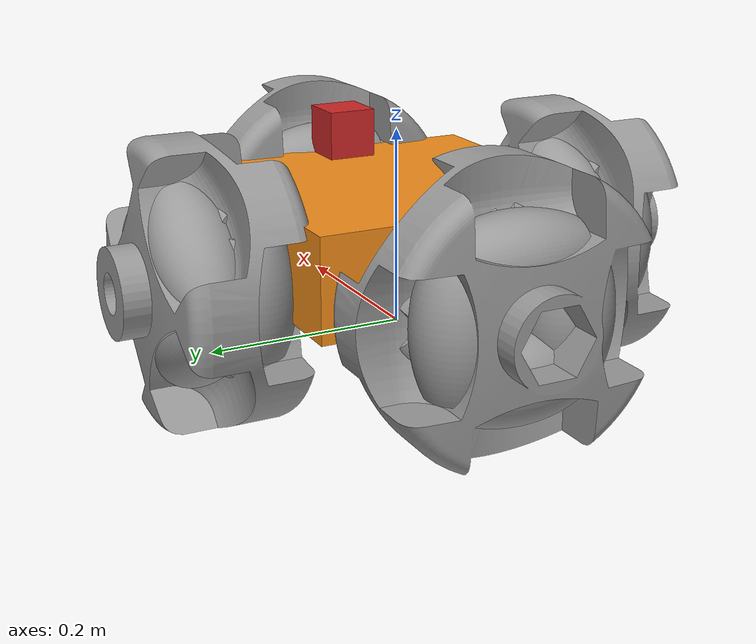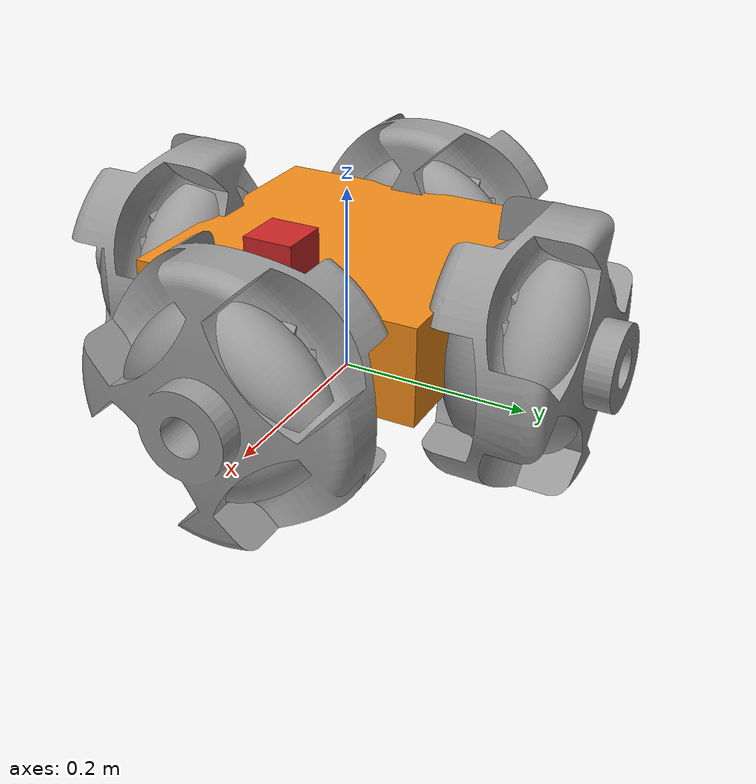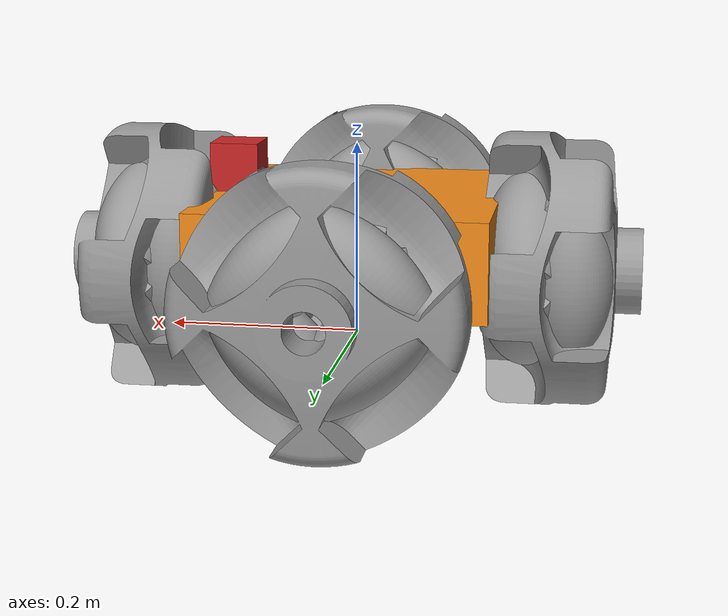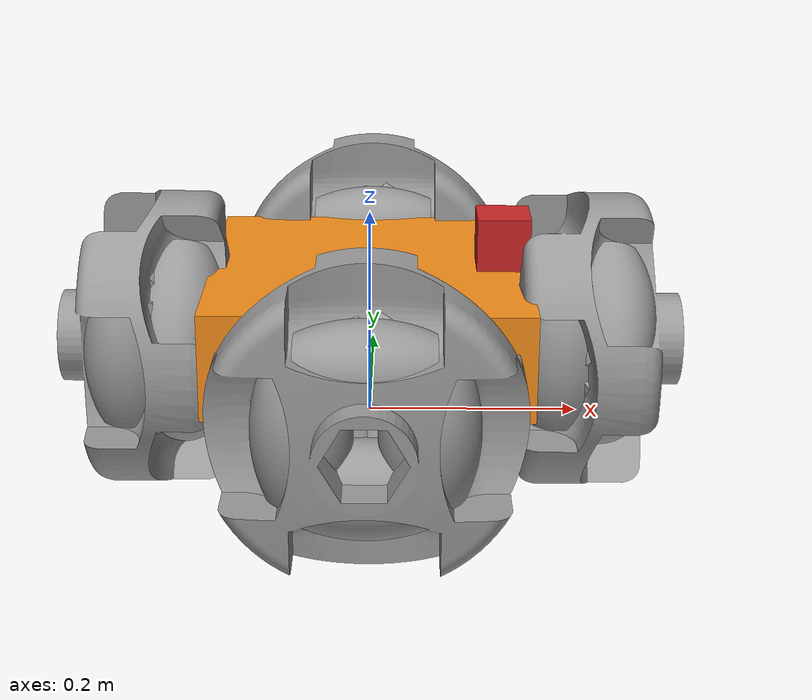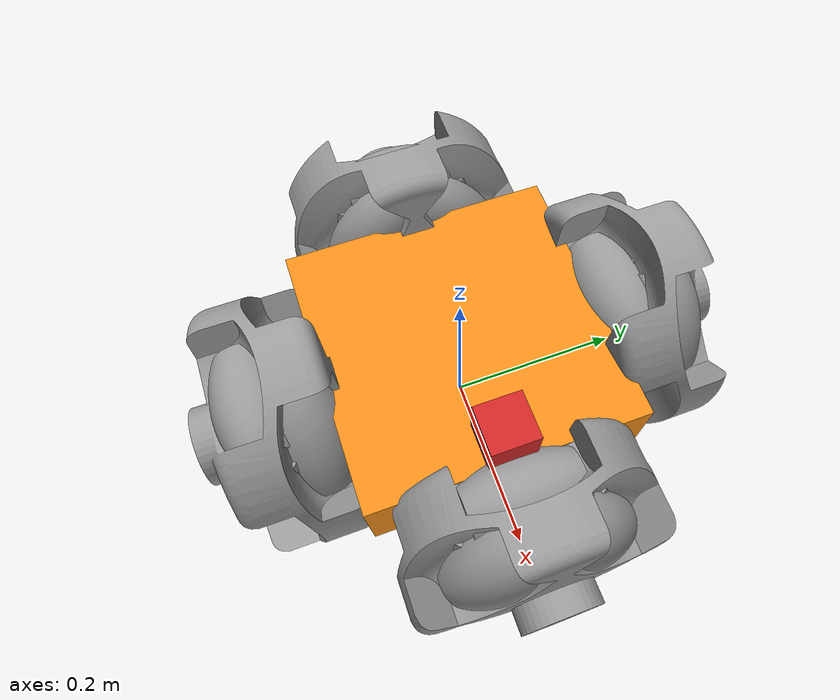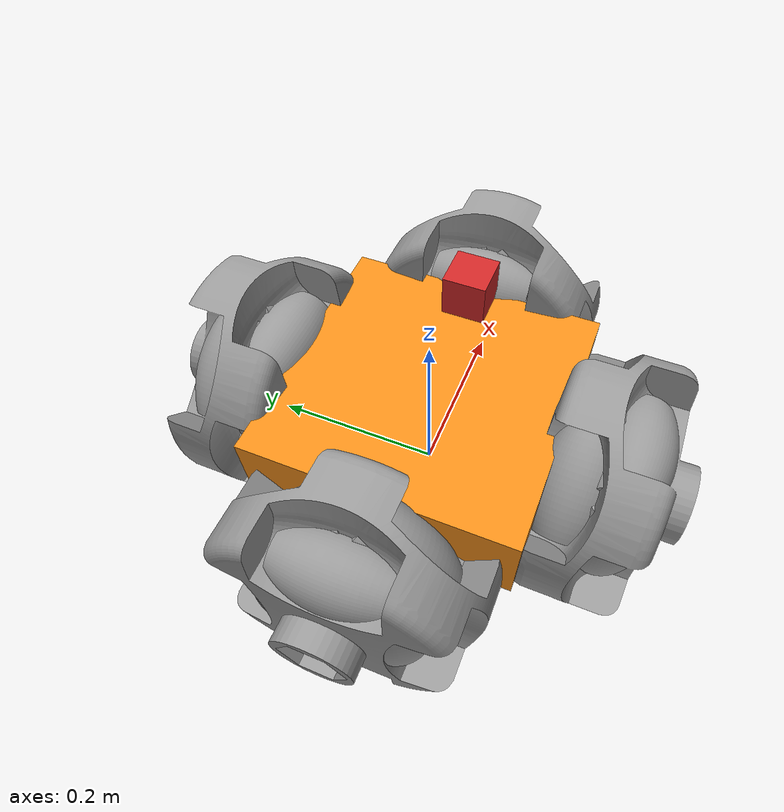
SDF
<?xml version='1.0'?>
<sdf version='1.7'>
  <model name='debug'>
    <link name='base_footprint'>
      <inertial>
        <pose>0 0 0 0 -0 0</pose>
        <mass>10</mass>
        <inertia>
          <ixx>2</ixx>
          <ixy>0</ixy>
          <ixz>0</ixz>
          <iyy>2</iyy>
          <iyz>0</iyz>
          <izz>2</izz>
        </inertia>
      </inertial>
      <self_collide>0</self_collide>
      <enable_wind>0</enable_wind>
      <kinematic>0</kinematic>
      <pose>-0 0 0.05 0 -0 0</pose>
      <gravity>1</gravity>
      <visual name='base_footprint_fixed_joint_lump__base_link_visual_1'>
        <pose>0 0 0.05 0 -0 0</pose>
        <geometry>
          <box>
            <size>0.3 0.3 0.1</size>
          </box>
        </geometry>
        <material>
          <script>
            <name>Gazebo/Orange</name>
            <uri>file://media/materials/scripts/gazebo.material</uri>
          </script>
          <shader type='pixel'>
            <normal_map>__default__</normal_map>
          </shader>
          <ambient>1 0.509 0.047 1</ambient>
          <diffuse>1 0.509 0.047 1</diffuse>
          <specular>0.5 0.5 0.5 1</specular>
          <emissive>0 0 0 1</emissive>
        </material>
        <transparency>0</transparency>
        <cast_shadows>1</cast_shadows>
      </visual>
      <visual name='base_footprint_fixed_joint_lump__camera_link_visual_2'>
        <pose>0.125 0 0.125 0 -0 0</pose>
        <geometry>
          <box>
            <size>0.05 0.05 0.05</size>
          </box>
        </geometry>
        <material>
          <script>
            <name>Gazebo/Red</name>
            <uri>file://media/materials/scripts/gazebo.material</uri>
          </script>
          <shader type='pixel'>
            <normal_map>__default__</normal_map>
          </shader>
          <ambient>1 0 0 1</ambient>
          <diffuse>1 0 0 1</diffuse>
          <specular>0.1 0.1 0.1 1</specular>
          <emissive>0 0 0 1</emissive>
        </material>
        <transparency>0</transparency>
        <cast_shadows>1</cast_shadows>
      </visual>
      <collision name='base_footprint_fixed_joint_lump__base_link_collision'>
        <laser_retro>0</laser_retro>
        <max_contacts>10</max_contacts>
        <pose>0 0 0.05 0 -0 0</pose>
        <geometry>
          <box>
            <size>0.3 0.3 0.1</size>
          </box>
        </geometry>
        <surface>
          <friction>
            <ode>
              <mu>1</mu>
              <mu2>1</mu2>
              <fdir1>0 0 0</fdir1>
              <slip1>0</slip1>
              <slip2>0</slip2>
            </ode>
            <torsional>
              <coefficient>1</coefficient>
              <patch_radius>0</patch_radius>
              <surface_radius>0</surface_radius>
              <use_patch_radius>1</use_patch_radius>
              <ode>
                <slip>0</slip>
              </ode>
            </torsional>
          </friction>
          <bounce>
            <restitution_coefficient>0</restitution_coefficient>
            <threshold>1e+06</threshold>
          </bounce>
          <contact>
            <collide_without_contact>0</collide_without_contact>
            <collide_without_contact_bitmask>1</collide_without_contact_bitmask>
            <collide_bitmask>1</collide_bitmask>
            <ode>
              <soft_cfm>0</soft_cfm>
              <soft_erp>0.2</soft_erp>
              <kp>1e+13</kp>
              <kd>1</kd>
              <max_vel>0.01</max_vel>
              <min_depth>0</min_depth>
            </ode>
            <bullet>
              <split_impulse>1</split_impulse>
              <split_impulse_penetration_threshold>-0.01</split_impulse_penetration_threshold>
              <soft_cfm>0</soft_cfm>
              <soft_erp>0.2</soft_erp>
              <kp>1e+13</kp>
              <kd>1</kd>
            </bullet>
          </contact>
        </surface>
      </collision>
      <collision name='base_footprint_fixed_joint_lump__camera_link_collision_1'>
        <laser_retro>0</laser_retro>
        <max_contacts>10</max_contacts>
        <pose>0.125 0 0.125 0 -0 0</pose>
        <geometry>
          <box>
            <size>0.05 0.05 0.05</size>
          </box>
        </geometry>
        <surface>
          <friction>
            <ode>
              <mu>0.2</mu>
              <mu2>0.2</mu2>
              <fdir1>0 0 0</fdir1>
              <slip1>0</slip1>
              <slip2>0</slip2>
            </ode>
            <torsional>
              <coefficient>1</coefficient>
              <patch_radius>0</patch_radius>
              <surface_radius>0</surface_radius>
              <use_patch_radius>1</use_patch_radius>
              <ode>
                <slip>0</slip>
              </ode>
            </torsional>
          </friction>
          <bounce>
            <restitution_coefficient>0</restitution_coefficient>
            <threshold>1e+06</threshold>
          </bounce>
          <contact>
            <collide_without_contact>0</collide_without_contact>
            <collide_without_contact_bitmask>1</collide_without_contact_bitmask>
            <collide_bitmask>1</collide_bitmask>
            <ode>
              <soft_cfm>0</soft_cfm>
              <soft_erp>0.2</soft_erp>
              <kp>1e+13</kp>
              <kd>1</kd>
              <max_vel>0.01</max_vel>
              <min_depth>0</min_depth>
            </ode>
            <bullet>
              <split_impulse>1</split_impulse>
              <split_impulse_penetration_threshold>-0.01</split_impulse_penetration_threshold>
              <soft_cfm>0</soft_cfm>
              <soft_erp>0.2</soft_erp>
              <kp>1e+13</kp>
              <kd>1</kd>
            </bullet>
          </contact>
        </surface>
      </collision>
    </link>
    <model name='wheel_1'>
      <pose>-0 -0.201 0.075 0 0 1.5708</pose>
      <link name='omni_wheel_rim_link'>
        <pose>0 0 0 0 -0 0</pose>
        <inertial>
          <mass>0.534902</mass>
          <inertia>
            <ixx>9.40333e-07</ixx>
            <ixy>0</ixy>
            <ixz>0</ixz>
            <iyy>6.63684e-07</iyy>
            <iyz>0</iyz>
            <izz>6.63684e-07</izz>
          </inertia>
          <pose>0 -0.000343 0 0 -0 0</pose>
        </inertial>
        <self_collide>0</self_collide>
        <kinematic>0</kinematic>
        <gravity>1</gravity>
        <visual name='visual'>
          <pose>0 0 0 0 -0 0</pose>
          <geometry>
            <mesh>
              <uri>model://omni_wheel/rim.stl</uri>
              <scale>4 4 4</scale>
            </mesh>
          </geometry>
          <material>
            <lighting>1</lighting>
            <script>
              <uri>file://media/materials/scripts/gazebo.material</uri>
              <name>Gazebo/Grey</name>
            </script>
            <ambient>0.3 0.3 0.3 1</ambient>
            <diffuse>0.7 0.7 0.7 1</diffuse>
            <specular>0.01 0.01 0.01 1</specular>
            <emissive>0 0 0 1</emissive>
            <shader type='vertex'>
              <normal_map>__default__</normal_map>
            </shader>
          </material>
          <transparency>0</transparency>
          <cast_shadows>1</cast_shadows>
        </visual>
        <collision name='collision'>
          <laser_retro>0</laser_retro>
          <max_contacts>10</max_contacts>
          <pose>0 0 0 0 -0 0</pose>
          <geometry>
            <mesh>
              <uri>model://omni_wheel/rim.stl</uri>
              <scale>4 4 4</scale>
            </mesh>
          </geometry>
          <surface>
            <friction>
              <ode>
                <mu>1</mu>
                <mu2>1</mu2>
                <fdir1>0 0 0</fdir1>
                <slip1>0</slip1>
                <slip2>0</slip2>
              </ode>
              <torsional>
                <coefficient>1</coefficient>
                <patch_radius>0</patch_radius>
                <surface_radius>0</surface_radius>
                <use_patch_radius>1</use_patch_radius>
                <ode>
                  <slip>0</slip>
                </ode>
              </torsional>
            </friction>
            <bounce>
              <restitution_coefficient>0</restitution_coefficient>
              <threshold>1e+06</threshold>
            </bounce>
            <contact>
              <collide_without_contact>0</collide_without_contact>
              <collide_without_contact_bitmask>1</collide_without_contact_bitmask>
              <collide_bitmask>1</collide_bitmask>
              <ode>
                <soft_cfm>0</soft_cfm>
                <soft_erp>0.2</soft_erp>
                <kp>1e+13</kp>
                <kd>1</kd>
                <max_vel>0.01</max_vel>
                <min_depth>0</min_depth>
              </ode>
              <bullet>
                <split_impulse>1</split_impulse>
                <split_impulse_penetration_threshold>-0.01</split_impulse_penetration_threshold>
                <soft_cfm>0</soft_cfm>
                <soft_erp>0.2</soft_erp>
                <kp>1e+13</kp>
                <kd>1</kd>
              </bullet>
            </contact>
          </surface>
        </collision>
        <enable_wind>0</enable_wind>
      </link>
      <link name='omni_wheel_roller_e_link'>
        <pose>-0.022 0.0542 0 0 -0 0</pose>
        <inertial>
          <mass>0.00113845</mass>
          <inertia>
            <ixx>2.53776e-08</ixx>
            <ixy>0</ixy>
            <ixz>0</ixz>
            <iyy>2.53776e-08</iyy>
            <iyz>0</iyz>
            <izz>1.47666e-08</izz>
          </inertia>
          <pose>0 0 0 0 -0 0</pose>
        </inertial>
        <self_collide>0</self_collide>
        <kinematic>0</kinematic>
        <visual name='visual'>
          <pose>0 0 0 0 -0 0</pose>
          <geometry>
            <mesh>
              <uri>model://omni_wheel/roller.stl</uri>
              <scale>4 4 4</scale>
            </mesh>
          </geometry>
          <material>
            <lighting>1</lighting>
            <script>
              <uri>file://media/materials/scripts/gazebo.material</uri>
              <name>Gazebo/Grey</name>
            </script>
            <ambient>0.03 0.03 0.03 1</ambient>
            <diffuse>0.07 0.07 0.07 1</diffuse>
            <specular>0.001 0.001 0.001 1</specular>
            <emissive>0 0 0 1</emissive>
            <shader type='vertex'>
              <normal_map>__default__</normal_map>
            </shader>
          </material>
          <transparency>0</transparency>
          <cast_shadows>1</cast_shadows>
        </visual>
        <collision name='collision'>
          <laser_retro>0</laser_retro>
          <max_contacts>10</max_contacts>
          <pose>0 0 0 0 -0 0</pose>
          <geometry>
            <mesh>
              <uri>model://omni_wheel/roller.stl</uri>
              <scale>4 4 4</scale>
            </mesh>
          </geometry>
          <surface>
            <friction>
              <ode>
                <mu>1</mu>
                <mu2>1</mu2>
                <fdir1>0 0 0</fdir1>
                <slip1>0</slip1>
                <slip2>0</slip2>
              </ode>
              <torsional>
                <coefficient>1</coefficient>
                <patch_radius>0</patch_radius>
                <surface_radius>0</surface_radius>
                <use_patch_radius>1</use_patch_radius>
                <ode>
                  <slip>0</slip>
                </ode>
              </torsional>
            </friction>
            <bounce>
              <restitution_coefficient>0</restitution_coefficient>
              <threshold>1e+06</threshold>
            </bounce>
            <contact>
              <collide_without_contact>0</collide_without_contact>
              <collide_without_contact_bitmask>1</collide_without_contact_bitmask>
              <collide_bitmask>1</collide_bitmask>
              <ode>
                <soft_cfm>0</soft_cfm>
                <soft_erp>0.2</soft_erp>
                <kp>1e+13</kp>
                <kd>1</kd>
                <max_vel>0.01</max_vel>
                <min_depth>0</min_depth>
              </ode>
              <bullet>
                <split_impulse>1</split_impulse>
                <split_impulse_penetration_threshold>-0.01</split_impulse_penetration_threshold>
                <soft_cfm>0</soft_cfm>
                <soft_erp>0.2</soft_erp>
                <kp>1e+13</kp>
                <kd>1</kd>
              </bullet>
            </contact>
          </surface>
        </collision>
        <enable_wind>0</enable_wind>
      </link>
      <link name='omni_wheel_roller_ne_link'>
        <pose>0.022 0.038324 0.038324 0.875398 -0 0</pose>
        <inertial>
          <mass>0.00113845</mass>
          <inertia>
            <ixx>2.53776e-08</ixx>
            <ixy>0</ixy>
            <ixz>0</ixz>
            <iyy>2.53776e-08</iyy>
            <iyz>0</iyz>
            <izz>1.47666e-08</izz>
          </inertia>
          <pose>0 0 0 0 -0 0</pose>
        </inertial>
        <self_collide>0</self_collide>
        <kinematic>0</kinematic>
        <visual name='visual'>
          <pose>0 0 0 0 -0 0</pose>
          <geometry>
            <mesh>
              <uri>model://omni_wheel/roller.stl</uri>
              <scale>4 4 4</scale>
            </mesh>
          </geometry>
          <material>
            <lighting>1</lighting>
            <script>
              <uri>file://media/materials/scripts/gazebo.material</uri>
              <name>Gazebo/Grey</name>
            </script>
            <ambient>0.03 0.03 0.03 1</ambient>
            <diffuse>0.07 0.07 0.07 1</diffuse>
            <specular>0.001 0.001 0.001 1</specular>
            <emissive>0 0 0 1</emissive>
            <shader type='vertex'>
              <normal_map>__default__</normal_map>
            </shader>
          </material>
          <transparency>0</transparency>
          <cast_shadows>1</cast_shadows>
        </visual>
        <collision name='collision'>
          <laser_retro>0</laser_retro>
          <max_contacts>10</max_contacts>
          <pose>0 0 0 0 -0 0</pose>
          <geometry>
            <mesh>
              <uri>model://omni_wheel/roller.stl</uri>
              <scale>4 4 4</scale>
            </mesh>
          </geometry>
          <surface>
            <friction>
              <ode>
                <mu>1</mu>
                <mu2>1</mu2>
                <fdir1>0 0 0</fdir1>
                <slip1>0</slip1>
                <slip2>0</slip2>
              </ode>
              <torsional>
                <coefficient>1</coefficient>
                <patch_radius>0</patch_radius>
                <surface_radius>0</surface_radius>
                <use_patch_radius>1</use_patch_radius>
                <ode>
                  <slip>0</slip>
                </ode>
              </torsional>
            </friction>
            <bounce>
              <restitution_coefficient>0</restitution_coefficient>
              <threshold>1e+06</threshold>
            </bounce>
            <contact>
              <collide_without_contact>0</collide_without_contact>
              <collide_without_contact_bitmask>1</collide_without_contact_bitmask>
              <collide_bitmask>1</collide_bitmask>
              <ode>
                <soft_cfm>0</soft_cfm>
                <soft_erp>0.2</soft_erp>
                <kp>1e+13</kp>
                <kd>1</kd>
                <max_vel>0.01</max_vel>
                <min_depth>0</min_depth>
              </ode>
              <bullet>
                <split_impulse>1</split_impulse>
                <split_impulse_penetration_threshold>-0.01</split_impulse_penetration_threshold>
                <soft_cfm>0</soft_cfm>
                <soft_erp>0.2</soft_erp>
                <kp>1e+13</kp>
                <kd>1</kd>
              </bullet>
            </contact>
          </surface>
        </collision>
        <enable_wind>0</enable_wind>
      </link>
      <link name='omni_wheel_roller_n_link'>
        <pose>-0.022 0 0.0542 1.5708 -0 0</pose>
        <inertial>
          <mass>0.00113845</mass>
          <inertia>
            <ixx>2.53776e-08</ixx>
            <ixy>0</ixy>
            <ixz>0</ixz>
            <iyy>2.53776e-08</iyy>
            <iyz>0</iyz>
            <izz>1.47666e-08</izz>
          </inertia>
          <pose>0 0 0 0 -0 0</pose>
        </inertial>
        <self_collide>0</self_collide>
        <kinematic>0</kinematic>
        <gravity>1</gravity>
        <visual name='visual'>
          <pose>0 0 0 0 -0 0</pose>
          <geometry>
            <mesh>
              <uri>model://omni_wheel/roller.stl</uri>
              <scale>4 4 4</scale>
            </mesh>
          </geometry>
          <material>
            <lighting>1</lighting>
            <script>
              <uri>file://media/materials/scripts/gazebo.material</uri>
              <name>Gazebo/Grey</name>
            </script>
            <ambient>0.03 0.03 0.03 1</ambient>
            <diffuse>0.07 0.07 0.07 1</diffuse>
            <specular>0.001 0.001 0.001 1</specular>
            <emissive>0 0 0 1</emissive>
            <shader type='vertex'>
              <normal_map>__default__</normal_map>
            </shader>
          </material>
          <transparency>0</transparency>
          <cast_shadows>1</cast_shadows>
        </visual>
        <collision name='collision'>
          <laser_retro>0</laser_retro>
          <max_contacts>10</max_contacts>
          <pose>0 0 0 0 -0 0</pose>
          <geometry>
            <mesh>
              <uri>model://omni_wheel/roller.stl</uri>
              <scale>4 4 4</scale>
            </mesh>
          </geometry>
          <surface>
            <friction>
              <ode>
                <mu>1</mu>
                <mu2>1</mu2>
                <fdir1>0 0 0</fdir1>
                <slip1>0</slip1>
                <slip2>0</slip2>
              </ode>
              <torsional>
                <coefficient>1</coefficient>
                <patch_radius>0</patch_radius>
                <surface_radius>0</surface_radius>
                <use_patch_radius>1</use_patch_radius>
                <ode>
                  <slip>0</slip>
                </ode>
              </torsional>
            </friction>
            <bounce>
              <restitution_coefficient>0</restitution_coefficient>
              <threshold>1e+06</threshold>
            </bounce>
            <contact>
              <collide_without_contact>0</collide_without_contact>
              <collide_without_contact_bitmask>1</collide_without_contact_bitmask>
              <collide_bitmask>1</collide_bitmask>
              <ode>
                <soft_cfm>0</soft_cfm>
                <soft_erp>0.2</soft_erp>
                <kp>1e+13</kp>
                <kd>1</kd>
                <max_vel>0.01</max_vel>
                <min_depth>0</min_depth>
              </ode>
              <bullet>
                <split_impulse>1</split_impulse>
                <split_impulse_penetration_threshold>-0.01</split_impulse_penetration_threshold>
                <soft_cfm>0</soft_cfm>
                <soft_erp>0.2</soft_erp>
                <kp>1e+13</kp>
                <kd>1</kd>
              </bullet>
            </contact>
          </surface>
        </collision>
        <enable_wind>0</enable_wind>
      </link>
      <link name='omni_wheel_roller_nw_link'>
        <pose>0.022 -0.038324 0.038324 2.35619 -0 0</pose>
        <inertial>
          <mass>0.00113845</mass>
          <inertia>
            <ixx>2.53776e-08</ixx>
            <ixy>0</ixy>
            <ixz>0</ixz>
            <iyy>2.53776e-08</iyy>
            <iyz>0</iyz>
            <izz>1.47666e-08</izz>
          </inertia>
          <pose>0 0 0 0 -0 0</pose>
        </inertial>
        <self_collide>0</self_collide>
        <kinematic>0</kinematic>
        <gravity>1</gravity>
        <visual name='visual'>
          <pose>0 0 0 0 -0 0</pose>
          <geometry>
            <mesh>
              <uri>model://omni_wheel/roller.stl</uri>
              <scale>4 4 4</scale>
            </mesh>
          </geometry>
          <material>
            <lighting>1</lighting>
            <script>
              <uri>file://media/materials/scripts/gazebo.material</uri>
              <name>Gazebo/Grey</name>
            </script>
            <ambient>0.03 0.03 0.03 1</ambient>
            <diffuse>0.07 0.07 0.07 1</diffuse>
            <specular>0.001 0.001 0.001 1</specular>
            <emissive>0 0 0 1</emissive>
            <shader type='vertex'>
              <normal_map>__default__</normal_map>
            </shader>
          </material>
          <transparency>0</transparency>
          <cast_shadows>1</cast_shadows>
        </visual>
        <collision name='collision'>
          <laser_retro>0</laser_retro>
          <max_contacts>10</max_contacts>
          <pose>0 0 0 0 -0 0</pose>
          <geometry>
            <mesh>
              <uri>model://omni_wheel/roller.stl</uri>
              <scale>4 4 4</scale>
            </mesh>
          </geometry>
          <surface>
            <friction>
              <ode>
                <mu>1</mu>
                <mu2>1</mu2>
                <fdir1>0 0 0</fdir1>
                <slip1>0</slip1>
                <slip2>0</slip2>
              </ode>
              <torsional>
                <coefficient>1</coefficient>
                <patch_radius>0</patch_radius>
                <surface_radius>0</surface_radius>
                <use_patch_radius>1</use_patch_radius>
                <ode>
                  <slip>0</slip>
                </ode>
              </torsional>
            </friction>
            <bounce>
              <restitution_coefficient>0</restitution_coefficient>
              <threshold>1e+06</threshold>
            </bounce>
            <contact>
              <collide_without_contact>0</collide_without_contact>
              <collide_without_contact_bitmask>1</collide_without_contact_bitmask>
              <collide_bitmask>1</collide_bitmask>
              <ode>
                <soft_cfm>0</soft_cfm>
                <soft_erp>0.2</soft_erp>
                <kp>1e+13</kp>
                <kd>1</kd>
                <max_vel>0.01</max_vel>
                <min_depth>0</min_depth>
              </ode>
              <bullet>
                <split_impulse>1</split_impulse>
                <split_impulse_penetration_threshold>-0.01</split_impulse_penetration_threshold>
                <soft_cfm>0</soft_cfm>
                <soft_erp>0.2</soft_erp>
                <kp>1e+13</kp>
                <kd>1</kd>
              </bullet>
            </contact>
          </surface>
        </collision>
        <enable_wind>0</enable_wind>
      </link>
      <link name='omni_wheel_roller_w_link'>
        <pose>-0.022 -0.0542 0 -3.14159 0 0</pose>
        <inertial>
          <mass>0.00113845</mass>
          <inertia>
            <ixx>2.53776e-08</ixx>
            <ixy>0</ixy>
            <ixz>0</ixz>
            <iyy>2.53776e-08</iyy>
            <iyz>0</iyz>
            <izz>1.47666e-08</izz>
          </inertia>
          <pose>0 0 0 0 -0 0</pose>
        </inertial>
        <self_collide>0</self_collide>
        <kinematic>0</kinematic>
        <gravity>1</gravity>
        <visual name='visual'>
          <pose>0 0 0 0 -0 0</pose>
          <geometry>
            <mesh>
              <uri>model://omni_wheel/roller.stl</uri>
              <scale>4 4 4</scale>
            </mesh>
          </geometry>
          <material>
            <lighting>1</lighting>
            <script>
              <uri>file://media/materials/scripts/gazebo.material</uri>
              <name>Gazebo/Grey</name>
            </script>
            <ambient>0.03 0.03 0.03 1</ambient>
            <diffuse>0.07 0.07 0.07 1</diffuse>
            <specular>0.001 0.001 0.001 1</specular>
            <emissive>0 0 0 1</emissive>
            <shader type='vertex'>
              <normal_map>__default__</normal_map>
            </shader>
          </material>
          <transparency>0</transparency>
          <cast_shadows>1</cast_shadows>
        </visual>
        <collision name='collision'>
          <laser_retro>0</laser_retro>
          <max_contacts>10</max_contacts>
          <pose>0 0 0 0 -0 0</pose>
          <geometry>
            <mesh>
              <uri>model://omni_wheel/roller.stl</uri>
              <scale>4 4 4</scale>
            </mesh>
          </geometry>
          <surface>
            <friction>
              <ode>
                <mu>1</mu>
                <mu2>1</mu2>
                <fdir1>0 0 0</fdir1>
                <slip1>0</slip1>
                <slip2>0</slip2>
              </ode>
              <torsional>
                <coefficient>1</coefficient>
                <patch_radius>0</patch_radius>
                <surface_radius>0</surface_radius>
                <use_patch_radius>1</use_patch_radius>
                <ode>
                  <slip>0</slip>
                </ode>
              </torsional>
            </friction>
            <bounce>
              <restitution_coefficient>0</restitution_coefficient>
              <threshold>1e+06</threshold>
            </bounce>
            <contact>
              <collide_without_contact>0</collide_without_contact>
              <collide_without_contact_bitmask>1</collide_without_contact_bitmask>
              <collide_bitmask>1</collide_bitmask>
              <ode>
                <soft_cfm>0</soft_cfm>
                <soft_erp>0.2</soft_erp>
                <kp>1e+13</kp>
                <kd>1</kd>
                <max_vel>0.01</max_vel>
                <min_depth>0</min_depth>
              </ode>
              <bullet>
                <split_impulse>1</split_impulse>
                <split_impulse_penetration_threshold>-0.01</split_impulse_penetration_threshold>
                <soft_cfm>0</soft_cfm>
                <soft_erp>0.2</soft_erp>
                <kp>1e+13</kp>
                <kd>1</kd>
              </bullet>
            </contact>
          </surface>
        </collision>
        <enable_wind>0</enable_wind>
      </link>
      <link name='omni_wheel_roller_sw_link'>
        <pose>0.022 -0.038324 -0.038324 -2.35619 0 0</pose>
        <inertial>
          <mass>0.00113845</mass>
          <inertia>
            <ixx>2.53776e-08</ixx>
            <ixy>0</ixy>
            <ixz>0</ixz>
            <iyy>2.53776e-08</iyy>
            <iyz>0</iyz>
            <izz>1.47666e-08</izz>
          </inertia>
          <pose>0 0 0 0 -0 0</pose>
        </inertial>
        <self_collide>0</self_collide>
        <kinematic>0</kinematic>
        <gravity>1</gravity>
        <visual name='visual'>
          <pose>0 0 0 0 -0 0</pose>
          <geometry>
            <mesh>
              <uri>model://omni_wheel/roller.stl</uri>
              <scale>4 4 4</scale>
            </mesh>
          </geometry>
          <material>
            <lighting>1</lighting>
            <script>
              <uri>file://media/materials/scripts/gazebo.material</uri>
              <name>Gazebo/Grey</name>
            </script>
            <ambient>0.03 0.03 0.03 1</ambient>
            <diffuse>0.07 0.07 0.07 1</diffuse>
            <specular>0.001 0.001 0.001 1</specular>
            <emissive>0 0 0 1</emissive>
            <shader type='vertex'>
              <normal_map>__default__</normal_map>
            </shader>
          </material>
          <transparency>0</transparency>
          <cast_shadows>1</cast_shadows>
        </visual>
        <collision name='collision'>
          <laser_retro>0</laser_retro>
          <max_contacts>10</max_contacts>
          <pose>0 0 0 0 -0 0</pose>
          <geometry>
            <mesh>
              <uri>model://omni_wheel/roller.stl</uri>
              <scale>4 4 4</scale>
            </mesh>
          </geometry>
          <surface>
            <friction>
              <ode>
                <mu>1</mu>
                <mu2>1</mu2>
                <fdir1>0 0 0</fdir1>
                <slip1>0</slip1>
                <slip2>0</slip2>
              </ode>
              <torsional>
                <coefficient>1</coefficient>
                <patch_radius>0</patch_radius>
                <surface_radius>0</surface_radius>
                <use_patch_radius>1</use_patch_radius>
                <ode>
                  <slip>0</slip>
                </ode>
              </torsional>
            </friction>
            <bounce>
              <restitution_coefficient>0</restitution_coefficient>
              <threshold>1e+06</threshold>
            </bounce>
            <contact>
              <collide_without_contact>0</collide_without_contact>
              <collide_without_contact_bitmask>1</collide_without_contact_bitmask>
              <collide_bitmask>1</collide_bitmask>
              <ode>
                <soft_cfm>0</soft_cfm>
                <soft_erp>0.2</soft_erp>
                <kp>1e+13</kp>
                <kd>1</kd>
                <max_vel>0.01</max_vel>
                <min_depth>0</min_depth>
              </ode>
              <bullet>
                <split_impulse>1</split_impulse>
                <split_impulse_penetration_threshold>-0.01</split_impulse_penetration_threshold>
                <soft_cfm>0</soft_cfm>
                <soft_erp>0.2</soft_erp>
                <kp>1e+13</kp>
                <kd>1</kd>
              </bullet>
            </contact>
          </surface>
        </collision>
        <enable_wind>0</enable_wind>
      </link>
      <link name='omni_wheel_roller_s_link'>
        <pose>-0.022 0 -0.0542 -1.5708 0 0</pose>
        <inertial>
          <mass>0.00113845</mass>
          <inertia>
            <ixx>2.53776e-08</ixx>
            <ixy>0</ixy>
            <ixz>0</ixz>
            <iyy>2.53776e-08</iyy>
            <iyz>0</iyz>
            <izz>1.47666e-08</izz>
          </inertia>
          <pose>0 0 0 0 -0 0</pose>
        </inertial>
        <self_collide>0</self_collide>
        <kinematic>0</kinematic>
        <gravity>1</gravity>
        <visual name='visual'>
          <pose>0 0 0 0 -0 0</pose>
          <geometry>
            <mesh>
              <uri>model://omni_wheel/roller.stl</uri>
              <scale>4 4 4</scale>
            </mesh>
          </geometry>
          <material>
            <lighting>1</lighting>
            <script>
              <uri>file://media/materials/scripts/gazebo.material</uri>
              <name>Gazebo/Grey</name>
            </script>
            <ambient>0.03 0.03 0.03 1</ambient>
            <diffuse>0.07 0.07 0.07 1</diffuse>
            <specular>0.001 0.001 0.001 1</specular>
            <emissive>0 0 0 1</emissive>
            <shader type='vertex'>
              <normal_map>__default__</normal_map>
            </shader>
          </material>
          <transparency>0</transparency>
          <cast_shadows>1</cast_shadows>
        </visual>
        <collision name='collision'>
          <laser_retro>0</laser_retro>
          <max_contacts>10</max_contacts>
          <pose>0 0 0 0 -0 0</pose>
          <geometry>
            <mesh>
              <uri>model://omni_wheel/roller.stl</uri>
              <scale>4 4 4</scale>
            </mesh>
          </geometry>
          <surface>
            <friction>
              <ode>
                <mu>1</mu>
                <mu2>1</mu2>
                <fdir1>0 0 0</fdir1>
                <slip1>0</slip1>
                <slip2>0</slip2>
              </ode>
              <torsional>
                <coefficient>1</coefficient>
                <patch_radius>0</patch_radius>
                <surface_radius>0</surface_radius>
                <use_patch_radius>1</use_patch_radius>
                <ode>
                  <slip>0</slip>
                </ode>
              </torsional>
            </friction>
            <bounce>
              <restitution_coefficient>0</restitution_coefficient>
              <threshold>1e+06</threshold>
            </bounce>
            <contact>
              <collide_without_contact>0</collide_without_contact>
              <collide_without_contact_bitmask>1</collide_without_contact_bitmask>
              <collide_bitmask>1</collide_bitmask>
              <ode>
                <soft_cfm>0</soft_cfm>
                <soft_erp>0.2</soft_erp>
                <kp>1e+13</kp>
                <kd>1</kd>
                <max_vel>0.01</max_vel>
                <min_depth>0</min_depth>
              </ode>
              <bullet>
                <split_impulse>1</split_impulse>
                <split_impulse_penetration_threshold>-0.01</split_impulse_penetration_threshold>
                <soft_cfm>0</soft_cfm>
                <soft_erp>0.2</soft_erp>
                <kp>1e+13</kp>
                <kd>1</kd>
              </bullet>
            </contact>
          </surface>
        </collision>
        <enable_wind>0</enable_wind>
      </link>
      <link name='omni_wheel_roller_se_link'>
        <pose>0.022 0.038324 -0.038324 -0.875398 0 0</pose>
        <inertial>
          <mass>0.00113845</mass>
          <inertia>
            <ixx>2.53776e-08</ixx>
            <ixy>0</ixy>
            <ixz>0</ixz>
            <iyy>2.53776e-08</iyy>
            <iyz>0</iyz>
            <izz>1.47666e-08</izz>
          </inertia>
          <pose>0 0 0 0 -0 0</pose>
        </inertial>
        <self_collide>0</self_collide>
        <kinematic>0</kinematic>
        <gravity>1</gravity>
        <visual name='visual'>
          <pose>0 0 0 0 -0 0</pose>
          <geometry>
            <mesh>
              <uri>model://omni_wheel/roller.stl</uri>
              <scale>4 4 4</scale>
            </mesh>
          </geometry>
          <material>
            <lighting>1</lighting>
            <script>
              <uri>file://media/materials/scripts/gazebo.material</uri>
              <name>Gazebo/Grey</name>
            </script>
            <ambient>0.03 0.03 0.03 1</ambient>
            <diffuse>0.07 0.07 0.07 1</diffuse>
            <specular>0.001 0.001 0.001 1</specular>
            <emissive>0 0 0 1</emissive>
            <shader type='vertex'>
              <normal_map>__default__</normal_map>
            </shader>
          </material>
          <transparency>0</transparency>
          <cast_shadows>1</cast_shadows>
        </visual>
        <collision name='collision'>
          <laser_retro>0</laser_retro>
          <max_contacts>10</max_contacts>
          <pose>0 0 0 0 -0 0</pose>
          <geometry>
            <mesh>
              <uri>model://omni_wheel/roller.stl</uri>
              <scale>4 4 4</scale>
            </mesh>
          </geometry>
          <surface>
            <friction>
              <ode>
                <mu>1</mu>
                <mu2>1</mu2>
                <fdir1>0 0 0</fdir1>
                <slip1>0</slip1>
                <slip2>0</slip2>
              </ode>
              <torsional>
                <coefficient>1</coefficient>
                <patch_radius>0</patch_radius>
                <surface_radius>0</surface_radius>
                <use_patch_radius>1</use_patch_radius>
                <ode>
                  <slip>0</slip>
                </ode>
              </torsional>
            </friction>
            <bounce>
              <restitution_coefficient>0</restitution_coefficient>
              <threshold>1e+06</threshold>
            </bounce>
            <contact>
              <collide_without_contact>0</collide_without_contact>
              <collide_without_contact_bitmask>1</collide_without_contact_bitmask>
              <collide_bitmask>1</collide_bitmask>
              <ode>
                <soft_cfm>0</soft_cfm>
                <soft_erp>0.2</soft_erp>
                <kp>1e+13</kp>
                <kd>1</kd>
                <max_vel>0.01</max_vel>
                <min_depth>0</min_depth>
              </ode>
              <bullet>
                <split_impulse>1</split_impulse>
                <split_impulse_penetration_threshold>-0.01</split_impulse_penetration_threshold>
                <soft_cfm>0</soft_cfm>
                <soft_erp>0.2</soft_erp>
                <kp>1e+13</kp>
                <kd>1</kd>
              </bullet>
            </contact>
          </surface>
        </collision>
        <enable_wind>0</enable_wind>
      </link>
      <joint name='omni_wheel_s_joint' type='revolute'>
        <parent>omni_wheel_rim_link</parent>
        <child>omni_wheel_roller_s_link</child>
        <pose>0 0 0 0 -0 1.5708</pose>
        <axis>
          <xyz>0 0 1</xyz>
          <limit>
            <lower>-1.79769e+308</lower>
            <upper>1.79769e+308</upper>
            <effort>-1</effort>
            <velocity>-1</velocity>
          </limit>
          <dynamics>
            <spring_reference>0</spring_reference>
            <spring_stiffness>0</spring_stiffness>
            <damping>0</damping>
            <friction>0</friction>
          </dynamics>

        </axis>
        <physics>
          <ode>
            <limit>
              <cfm>0</cfm>
              <erp>0.2</erp>
            </limit>
            <suspension>
              <cfm>0</cfm>
              <erp>0.2</erp>
            </suspension>
          </ode>
        </physics>
      </joint>
      <joint name='omni_wheel_se_joint' type='revolute'>
        <parent>omni_wheel_rim_link</parent>
        <child>omni_wheel_roller_se_link</child>
        <pose>0 0 0 0 -0 1.5708</pose>
        <axis>
          <xyz>0 0 1</xyz>
          <limit>
            <lower>-1.79769e+308</lower>
            <upper>1.79769e+308</upper>
            <effort>-1</effort>
            <velocity>-1</velocity>
          </limit>
          <dynamics>
            <spring_reference>0</spring_reference>
            <spring_stiffness>0</spring_stiffness>
            <damping>0</damping>
            <friction>0</friction>
          </dynamics>

        </axis>
        <physics>
          <ode>
            <limit>
              <cfm>0</cfm>
              <erp>0.2</erp>
            </limit>
            <suspension>
              <cfm>0</cfm>
              <erp>0.2</erp>
            </suspension>
          </ode>
        </physics>
      </joint>
      <joint name='omni_wheel_e_joint' type='revolute'>
        <parent>omni_wheel_rim_link</parent>
        <child>omni_wheel_roller_e_link</child>
        <pose>0 0 0 0 -0 1.5708</pose>
        <axis>
          <xyz>0 0 1</xyz>
          <limit>
            <lower>-1.79769e+308</lower>
            <upper>1.79769e+308</upper>
            <effort>-1</effort>
            <velocity>-1</velocity>
          </limit>
          <dynamics>
            <spring_reference>0</spring_reference>
            <spring_stiffness>0</spring_stiffness>
            <damping>0</damping>
            <friction>0</friction>
          </dynamics>

        </axis>
        <physics>
          <ode>
            <limit>
              <cfm>0</cfm>
              <erp>0.2</erp>
            </limit>
            <suspension>
              <cfm>0</cfm>
              <erp>0.2</erp>
            </suspension>
          </ode>
        </physics>
      </joint>
      <joint name='omni_wheel_ne_joint' type='revolute'>
        <parent>omni_wheel_rim_link</parent>
        <child>omni_wheel_roller_ne_link</child>
        <pose>0 0 0 0 -0 1.5708</pose>
        <axis>
          <xyz>0 0 1</xyz>
          <limit>
            <lower>-1.79769e+308</lower>
            <upper>1.79769e+308</upper>
            <effort>-1</effort>
            <velocity>-1</velocity>
          </limit>
          <dynamics>
            <spring_reference>0</spring_reference>
            <spring_stiffness>0</spring_stiffness>
            <damping>0</damping>
            <friction>0</friction>
          </dynamics>

        </axis>
        <physics>
          <ode>
            <limit>
              <cfm>0</cfm>
              <erp>0.2</erp>
            </limit>
            <suspension>
              <cfm>0</cfm>
              <erp>0.2</erp>
            </suspension>
          </ode>
        </physics>
      </joint>
      <joint name='omni_wheel_n_joint' type='revolute'>
        <parent>omni_wheel_rim_link</parent>
        <child>omni_wheel_roller_n_link</child>
        <pose>0 0 0 0 -0 1.5708</pose>
        <axis>
          <xyz>0 0 1</xyz>
          <limit>
            <lower>-1.79769e+308</lower>
            <upper>1.79769e+308</upper>
            <effort>-1</effort>
            <velocity>-1</velocity>
          </limit>
          <dynamics>
            <spring_reference>0</spring_reference>
            <spring_stiffness>0</spring_stiffness>
            <damping>0</damping>
            <friction>0</friction>
          </dynamics>

        </axis>
        <physics>
          <ode>
            <limit>
              <cfm>0</cfm>
              <erp>0.2</erp>
            </limit>
            <suspension>
              <cfm>0</cfm>
              <erp>0.2</erp>
            </suspension>
          </ode>
        </physics>
      </joint>
      <joint name='omni_wheel_nw_joint' type='revolute'>
        <parent>omni_wheel_rim_link</parent>
        <child>omni_wheel_roller_nw_link</child>
        <pose>0 0 0 0 -0 1.5708</pose>
        <axis>
          <xyz>0 0 1</xyz>
          <limit>
            <lower>-1.79769e+308</lower>
            <upper>1.79769e+308</upper>
            <effort>-1</effort>
            <velocity>-1</velocity>
          </limit>
          <dynamics>
            <spring_reference>0</spring_reference>
            <spring_stiffness>0</spring_stiffness>
            <damping>0</damping>
            <friction>0</friction>
          </dynamics>

        </axis>
        <physics>
          <ode>
            <limit>
              <cfm>0</cfm>
              <erp>0.2</erp>
            </limit>
            <suspension>
              <cfm>0</cfm>
              <erp>0.2</erp>
            </suspension>
          </ode>
        </physics>
      </joint>
      <joint name='omni_wheel_w_joint' type='revolute'>
        <parent>omni_wheel_rim_link</parent>
        <child>omni_wheel_roller_w_link</child>
        <pose>0 0 0 0 -0 1.5708</pose>
        <axis>
          <xyz>0 0 1</xyz>
          <limit>
            <lower>-1.79769e+308</lower>
            <upper>1.79769e+308</upper>
            <effort>-1</effort>
            <velocity>-1</velocity>
          </limit>
          <dynamics>
            <spring_reference>0</spring_reference>
            <spring_stiffness>0</spring_stiffness>
            <damping>0</damping>
            <friction>0</friction>
          </dynamics>

        </axis>
        <physics>
          <ode>
            <limit>
              <cfm>0</cfm>
              <erp>0.2</erp>
            </limit>
            <suspension>
              <cfm>0</cfm>
              <erp>0.2</erp>
            </suspension>
          </ode>
        </physics>
      </joint>
      <joint name='omni_wheel_sw_joint' type='revolute'>
        <parent>omni_wheel_rim_link</parent>
        <child>omni_wheel_roller_sw_link</child>
        <pose>0 0 0 0 -0 1.5708</pose>
        <axis>
          <xyz>0 0 1</xyz>
          <limit>
            <lower>-1.79769e+308</lower>
            <upper>1.79769e+308</upper>
            <effort>-1</effort>
            <velocity>-1</velocity>
          </limit>
          <dynamics>
            <spring_reference>0</spring_reference>
            <spring_stiffness>0</spring_stiffness>
            <damping>0</damping>
            <friction>0</friction>
          </dynamics>

        </axis>
        <physics>
          <ode>
            <limit>
              <cfm>0</cfm>
              <erp>0.2</erp>
            </limit>
            <suspension>
              <cfm>0</cfm>
              <erp>0.2</erp>
            </suspension>
          </ode>
        </physics>
      </joint>
      <static>0</static>
      <allow_auto_disable>1</allow_auto_disable>
    </model>
    <model name='wheel_2'>
      <pose>-0 0.201 0.075 0 0 1.5708</pose>
      <link name='omni_wheel_rim_link'>
        <pose>0 0 0 0 -0 0</pose>
        <inertial>
          <mass>0.534902</mass>
          <inertia>
            <ixx>9.40333e-07</ixx>
            <ixy>0</ixy>
            <ixz>0</ixz>
            <iyy>6.63684e-07</iyy>
            <iyz>0</iyz>
            <izz>6.63684e-07</izz>
          </inertia>
          <pose>0 -0.000343 0 0 -0 0</pose>
        </inertial>
        <self_collide>0</self_collide>
        <kinematic>0</kinematic>
        <gravity>1</gravity>
        <visual name='visual'>
          <pose>0 0 0 0 -0 0</pose>
          <geometry>
            <mesh>
              <uri>model://omni_wheel/rim.stl</uri>
              <scale>4 4 4</scale>
            </mesh>
          </geometry>
          <material>
            <lighting>1</lighting>
            <script>
              <uri>file://media/materials/scripts/gazebo.material</uri>
              <name>Gazebo/Grey</name>
            </script>
            <ambient>0.3 0.3 0.3 1</ambient>
            <diffuse>0.7 0.7 0.7 1</diffuse>
            <specular>0.01 0.01 0.01 1</specular>
            <emissive>0 0 0 1</emissive>
            <shader type='vertex'>
              <normal_map>__default__</normal_map>
            </shader>
          </material>
          <transparency>0</transparency>
          <cast_shadows>1</cast_shadows>
        </visual>
        <collision name='collision'>
          <laser_retro>0</laser_retro>
          <max_contacts>10</max_contacts>
          <pose>0 0 0 0 -0 0</pose>
          <geometry>
            <mesh>
              <uri>model://omni_wheel/rim.stl</uri>
              <scale>4 4 4</scale>
            </mesh>
          </geometry>
          <surface>
            <friction>
              <ode>
                <mu>1</mu>
                <mu2>1</mu2>
                <fdir1>0 0 0</fdir1>
                <slip1>0</slip1>
                <slip2>0</slip2>
              </ode>
              <torsional>
                <coefficient>1</coefficient>
                <patch_radius>0</patch_radius>
                <surface_radius>0</surface_radius>
                <use_patch_radius>1</use_patch_radius>
                <ode>
                  <slip>0</slip>
                </ode>
              </torsional>
            </friction>
            <bounce>
              <restitution_coefficient>0</restitution_coefficient>
              <threshold>1e+06</threshold>
            </bounce>
            <contact>
              <collide_without_contact>0</collide_without_contact>
              <collide_without_contact_bitmask>1</collide_without_contact_bitmask>
              <collide_bitmask>1</collide_bitmask>
              <ode>
                <soft_cfm>0</soft_cfm>
                <soft_erp>0.2</soft_erp>
                <kp>1e+13</kp>
                <kd>1</kd>
                <max_vel>0.01</max_vel>
                <min_depth>0</min_depth>
              </ode>
              <bullet>
                <split_impulse>1</split_impulse>
                <split_impulse_penetration_threshold>-0.01</split_impulse_penetration_threshold>
                <soft_cfm>0</soft_cfm>
                <soft_erp>0.2</soft_erp>
                <kp>1e+13</kp>
                <kd>1</kd>
              </bullet>
            </contact>
          </surface>
        </collision>
        <enable_wind>0</enable_wind>
      </link>
      <link name='omni_wheel_roller_e_link'>
        <pose>-0.022 0.0542 0 0 -0 0</pose>
        <inertial>
          <mass>0.00113845</mass>
          <inertia>
            <ixx>2.53776e-08</ixx>
            <ixy>0</ixy>
            <ixz>0</ixz>
            <iyy>2.53776e-08</iyy>
            <iyz>0</iyz>
            <izz>1.47666e-08</izz>
          </inertia>
          <pose>0 0 0 0 -0 0</pose>
        </inertial>
        <self_collide>0</self_collide>
        <kinematic>0</kinematic>
        <visual name='visual'>
          <pose>0 0 0 0 -0 0</pose>
          <geometry>
            <mesh>
              <uri>model://omni_wheel/roller.stl</uri>
              <scale>4 4 4</scale>
            </mesh>
          </geometry>
          <material>
            <lighting>1</lighting>
            <script>
              <uri>file://media/materials/scripts/gazebo.material</uri>
              <name>Gazebo/Grey</name>
            </script>
            <ambient>0.03 0.03 0.03 1</ambient>
            <diffuse>0.07 0.07 0.07 1</diffuse>
            <specular>0.001 0.001 0.001 1</specular>
            <emissive>0 0 0 1</emissive>
            <shader type='vertex'>
              <normal_map>__default__</normal_map>
            </shader>
          </material>
          <transparency>0</transparency>
          <cast_shadows>1</cast_shadows>
        </visual>
        <collision name='collision'>
          <laser_retro>0</laser_retro>
          <max_contacts>10</max_contacts>
          <pose>0 0 0 0 -0 0</pose>
          <geometry>
            <mesh>
              <uri>model://omni_wheel/roller.stl</uri>
              <scale>4 4 4</scale>
            </mesh>
          </geometry>
          <surface>
            <friction>
              <ode>
                <mu>1</mu>
                <mu2>1</mu2>
                <fdir1>0 0 0</fdir1>
                <slip1>0</slip1>
                <slip2>0</slip2>
              </ode>
              <torsional>
                <coefficient>1</coefficient>
                <patch_radius>0</patch_radius>
                <surface_radius>0</surface_radius>
                <use_patch_radius>1</use_patch_radius>
                <ode>
                  <slip>0</slip>
                </ode>
              </torsional>
            </friction>
            <bounce>
              <restitution_coefficient>0</restitution_coefficient>
              <threshold>1e+06</threshold>
            </bounce>
            <contact>
              <collide_without_contact>0</collide_without_contact>
              <collide_without_contact_bitmask>1</collide_without_contact_bitmask>
              <collide_bitmask>1</collide_bitmask>
              <ode>
                <soft_cfm>0</soft_cfm>
                <soft_erp>0.2</soft_erp>
                <kp>1e+13</kp>
                <kd>1</kd>
                <max_vel>0.01</max_vel>
                <min_depth>0</min_depth>
              </ode>
              <bullet>
                <split_impulse>1</split_impulse>
                <split_impulse_penetration_threshold>-0.01</split_impulse_penetration_threshold>
                <soft_cfm>0</soft_cfm>
                <soft_erp>0.2</soft_erp>
                <kp>1e+13</kp>
                <kd>1</kd>
              </bullet>
            </contact>
          </surface>
        </collision>
        <enable_wind>0</enable_wind>
      </link>
      <link name='omni_wheel_roller_ne_link'>
        <pose>0.022 0.038324 0.038324 0.875398 -0 0</pose>
        <inertial>
          <mass>0.00113845</mass>
          <inertia>
            <ixx>2.53776e-08</ixx>
            <ixy>0</ixy>
            <ixz>0</ixz>
            <iyy>2.53776e-08</iyy>
            <iyz>0</iyz>
            <izz>1.47666e-08</izz>
          </inertia>
          <pose>0 0 0 0 -0 0</pose>
        </inertial>
        <self_collide>0</self_collide>
        <kinematic>0</kinematic>
        <visual name='visual'>
          <pose>0 0 0 0 -0 0</pose>
          <geometry>
            <mesh>
              <uri>model://omni_wheel/roller.stl</uri>
              <scale>4 4 4</scale>
            </mesh>
          </geometry>
          <material>
            <lighting>1</lighting>
            <script>
              <uri>file://media/materials/scripts/gazebo.material</uri>
              <name>Gazebo/Grey</name>
            </script>
            <ambient>0.03 0.03 0.03 1</ambient>
            <diffuse>0.07 0.07 0.07 1</diffuse>
            <specular>0.001 0.001 0.001 1</specular>
            <emissive>0 0 0 1</emissive>
            <shader type='vertex'>
              <normal_map>__default__</normal_map>
            </shader>
          </material>
          <transparency>0</transparency>
          <cast_shadows>1</cast_shadows>
        </visual>
        <collision name='collision'>
          <laser_retro>0</laser_retro>
          <max_contacts>10</max_contacts>
          <pose>0 0 0 0 -0 0</pose>
          <geometry>
            <mesh>
              <uri>model://omni_wheel/roller.stl</uri>
              <scale>4 4 4</scale>
            </mesh>
          </geometry>
          <surface>
            <friction>
              <ode>
                <mu>1</mu>
                <mu2>1</mu2>
                <fdir1>0 0 0</fdir1>
                <slip1>0</slip1>
                <slip2>0</slip2>
              </ode>
              <torsional>
                <coefficient>1</coefficient>
                <patch_radius>0</patch_radius>
                <surface_radius>0</surface_radius>
                <use_patch_radius>1</use_patch_radius>
                <ode>
                  <slip>0</slip>
                </ode>
              </torsional>
            </friction>
            <bounce>
              <restitution_coefficient>0</restitution_coefficient>
              <threshold>1e+06</threshold>
            </bounce>
            <contact>
              <collide_without_contact>0</collide_without_contact>
              <collide_without_contact_bitmask>1</collide_without_contact_bitmask>
              <collide_bitmask>1</collide_bitmask>
              <ode>
                <soft_cfm>0</soft_cfm>
                <soft_erp>0.2</soft_erp>
                <kp>1e+13</kp>
                <kd>1</kd>
                <max_vel>0.01</max_vel>
                <min_depth>0</min_depth>
              </ode>
              <bullet>
                <split_impulse>1</split_impulse>
                <split_impulse_penetration_threshold>-0.01</split_impulse_penetration_threshold>
                <soft_cfm>0</soft_cfm>
                <soft_erp>0.2</soft_erp>
                <kp>1e+13</kp>
                <kd>1</kd>
              </bullet>
            </contact>
          </surface>
        </collision>
        <enable_wind>0</enable_wind>
      </link>
      <link name='omni_wheel_roller_n_link'>
        <pose>-0.022 0 0.0542 1.5708 -0 0</pose>
        <inertial>
          <mass>0.00113845</mass>
          <inertia>
            <ixx>2.53776e-08</ixx>
            <ixy>0</ixy>
            <ixz>0</ixz>
            <iyy>2.53776e-08</iyy>
            <iyz>0</iyz>
            <izz>1.47666e-08</izz>
          </inertia>
          <pose>0 0 0 0 -0 0</pose>
        </inertial>
        <self_collide>0</self_collide>
        <kinematic>0</kinematic>
        <gravity>1</gravity>
        <visual name='visual'>
          <pose>0 0 0 0 -0 0</pose>
          <geometry>
            <mesh>
              <uri>model://omni_wheel/roller.stl</uri>
              <scale>4 4 4</scale>
            </mesh>
          </geometry>
          <material>
            <lighting>1</lighting>
            <script>
              <uri>file://media/materials/scripts/gazebo.material</uri>
              <name>Gazebo/Grey</name>
            </script>
            <ambient>0.03 0.03 0.03 1</ambient>
            <diffuse>0.07 0.07 0.07 1</diffuse>
            <specular>0.001 0.001 0.001 1</specular>
            <emissive>0 0 0 1</emissive>
            <shader type='vertex'>
              <normal_map>__default__</normal_map>
            </shader>
          </material>
          <transparency>0</transparency>
          <cast_shadows>1</cast_shadows>
        </visual>
        <collision name='collision'>
          <laser_retro>0</laser_retro>
          <max_contacts>10</max_contacts>
          <pose>0 0 0 0 -0 0</pose>
          <geometry>
            <mesh>
              <uri>model://omni_wheel/roller.stl</uri>
              <scale>4 4 4</scale>
            </mesh>
          </geometry>
          <surface>
            <friction>
              <ode>
                <mu>1</mu>
                <mu2>1</mu2>
                <fdir1>0 0 0</fdir1>
                <slip1>0</slip1>
                <slip2>0</slip2>
              </ode>
              <torsional>
                <coefficient>1</coefficient>
                <patch_radius>0</patch_radius>
                <surface_radius>0</surface_radius>
                <use_patch_radius>1</use_patch_radius>
                <ode>
                  <slip>0</slip>
                </ode>
              </torsional>
            </friction>
            <bounce>
              <restitution_coefficient>0</restitution_coefficient>
              <threshold>1e+06</threshold>
            </bounce>
            <contact>
              <collide_without_contact>0</collide_without_contact>
              <collide_without_contact_bitmask>1</collide_without_contact_bitmask>
              <collide_bitmask>1</collide_bitmask>
              <ode>
                <soft_cfm>0</soft_cfm>
                <soft_erp>0.2</soft_erp>
                <kp>1e+13</kp>
                <kd>1</kd>
                <max_vel>0.01</max_vel>
                <min_depth>0</min_depth>
              </ode>
              <bullet>
                <split_impulse>1</split_impulse>
                <split_impulse_penetration_threshold>-0.01</split_impulse_penetration_threshold>
                <soft_cfm>0</soft_cfm>
                <soft_erp>0.2</soft_erp>
                <kp>1e+13</kp>
                <kd>1</kd>
              </bullet>
            </contact>
          </surface>
        </collision>
        <enable_wind>0</enable_wind>
      </link>
      <link name='omni_wheel_roller_nw_link'>
        <pose>0.022 -0.038324 0.038324 2.35619 -0 0</pose>
        <inertial>
          <mass>0.00113845</mass>
          <inertia>
            <ixx>2.53776e-08</ixx>
            <ixy>0</ixy>
            <ixz>0</ixz>
            <iyy>2.53776e-08</iyy>
            <iyz>0</iyz>
            <izz>1.47666e-08</izz>
          </inertia>
          <pose>0 0 0 0 -0 0</pose>
        </inertial>
        <self_collide>0</self_collide>
        <kinematic>0</kinematic>
        <gravity>1</gravity>
        <visual name='visual'>
          <pose>0 0 0 0 -0 0</pose>
          <geometry>
            <mesh>
              <uri>model://omni_wheel/roller.stl</uri>
              <scale>4 4 4</scale>
            </mesh>
          </geometry>
          <material>
            <lighting>1</lighting>
            <script>
              <uri>file://media/materials/scripts/gazebo.material</uri>
              <name>Gazebo/Grey</name>
            </script>
            <ambient>0.03 0.03 0.03 1</ambient>
            <diffuse>0.07 0.07 0.07 1</diffuse>
            <specular>0.001 0.001 0.001 1</specular>
            <emissive>0 0 0 1</emissive>
            <shader type='vertex'>
              <normal_map>__default__</normal_map>
            </shader>
          </material>
          <transparency>0</transparency>
          <cast_shadows>1</cast_shadows>
        </visual>
        <collision name='collision'>
          <laser_retro>0</laser_retro>
          <max_contacts>10</max_contacts>
          <pose>0 0 0 0 -0 0</pose>
          <geometry>
            <mesh>
              <uri>model://omni_wheel/roller.stl</uri>
              <scale>4 4 4</scale>
            </mesh>
          </geometry>
          <surface>
            <friction>
              <ode>
                <mu>1</mu>
                <mu2>1</mu2>
                <fdir1>0 0 0</fdir1>
                <slip1>0</slip1>
                <slip2>0</slip2>
              </ode>
              <torsional>
                <coefficient>1</coefficient>
                <patch_radius>0</patch_radius>
                <surface_radius>0</surface_radius>
                <use_patch_radius>1</use_patch_radius>
                <ode>
                  <slip>0</slip>
                </ode>
              </torsional>
            </friction>
            <bounce>
              <restitution_coefficient>0</restitution_coefficient>
              <threshold>1e+06</threshold>
            </bounce>
            <contact>
              <collide_without_contact>0</collide_without_contact>
              <collide_without_contact_bitmask>1</collide_without_contact_bitmask>
              <collide_bitmask>1</collide_bitmask>
              <ode>
                <soft_cfm>0</soft_cfm>
                <soft_erp>0.2</soft_erp>
                <kp>1e+13</kp>
                <kd>1</kd>
                <max_vel>0.01</max_vel>
                <min_depth>0</min_depth>
              </ode>
              <bullet>
                <split_impulse>1</split_impulse>
                <split_impulse_penetration_threshold>-0.01</split_impulse_penetration_threshold>
                <soft_cfm>0</soft_cfm>
                <soft_erp>0.2</soft_erp>
                <kp>1e+13</kp>
                <kd>1</kd>
              </bullet>
            </contact>
          </surface>
        </collision>
        <enable_wind>0</enable_wind>
      </link>
      <link name='omni_wheel_roller_w_link'>
        <pose>-0.022 -0.0542 0 -3.14159 0 0</pose>
        <inertial>
          <mass>0.00113845</mass>
          <inertia>
            <ixx>2.53776e-08</ixx>
            <ixy>0</ixy>
            <ixz>0</ixz>
            <iyy>2.53776e-08</iyy>
            <iyz>0</iyz>
            <izz>1.47666e-08</izz>
          </inertia>
          <pose>0 0 0 0 -0 0</pose>
        </inertial>
        <self_collide>0</self_collide>
        <kinematic>0</kinematic>
        <gravity>1</gravity>
        <visual name='visual'>
          <pose>0 0 0 0 -0 0</pose>
          <geometry>
            <mesh>
              <uri>model://omni_wheel/roller.stl</uri>
              <scale>4 4 4</scale>
            </mesh>
          </geometry>
          <material>
            <lighting>1</lighting>
            <script>
              <uri>file://media/materials/scripts/gazebo.material</uri>
              <name>Gazebo/Grey</name>
            </script>
            <ambient>0.03 0.03 0.03 1</ambient>
            <diffuse>0.07 0.07 0.07 1</diffuse>
            <specular>0.001 0.001 0.001 1</specular>
            <emissive>0 0 0 1</emissive>
            <shader type='vertex'>
              <normal_map>__default__</normal_map>
            </shader>
          </material>
          <transparency>0</transparency>
          <cast_shadows>1</cast_shadows>
        </visual>
        <collision name='collision'>
          <laser_retro>0</laser_retro>
          <max_contacts>10</max_contacts>
          <pose>0 0 0 0 -0 0</pose>
          <geometry>
            <mesh>
              <uri>model://omni_wheel/roller.stl</uri>
              <scale>4 4 4</scale>
            </mesh>
          </geometry>
          <surface>
            <friction>
              <ode>
                <mu>1</mu>
                <mu2>1</mu2>
                <fdir1>0 0 0</fdir1>
                <slip1>0</slip1>
                <slip2>0</slip2>
              </ode>
              <torsional>
                <coefficient>1</coefficient>
                <patch_radius>0</patch_radius>
                <surface_radius>0</surface_radius>
                <use_patch_radius>1</use_patch_radius>
                <ode>
                  <slip>0</slip>
                </ode>
              </torsional>
            </friction>
            <bounce>
              <restitution_coefficient>0</restitution_coefficient>
              <threshold>1e+06</threshold>
            </bounce>
            <contact>
              <collide_without_contact>0</collide_without_contact>
              <collide_without_contact_bitmask>1</collide_without_contact_bitmask>
              <collide_bitmask>1</collide_bitmask>
              <ode>
                <soft_cfm>0</soft_cfm>
                <soft_erp>0.2</soft_erp>
                <kp>1e+13</kp>
                <kd>1</kd>
                <max_vel>0.01</max_vel>
                <min_depth>0</min_depth>
              </ode>
              <bullet>
                <split_impulse>1</split_impulse>
                <split_impulse_penetration_threshold>-0.01</split_impulse_penetration_threshold>
                <soft_cfm>0</soft_cfm>
                <soft_erp>0.2</soft_erp>
                <kp>1e+13</kp>
                <kd>1</kd>
              </bullet>
            </contact>
          </surface>
        </collision>
        <enable_wind>0</enable_wind>
      </link>
      <link name='omni_wheel_roller_sw_link'>
        <pose>0.022 -0.038324 -0.038324 -2.35619 0 0</pose>
        <inertial>
          <mass>0.00113845</mass>
          <inertia>
            <ixx>2.53776e-08</ixx>
            <ixy>0</ixy>
            <ixz>0</ixz>
            <iyy>2.53776e-08</iyy>
            <iyz>0</iyz>
            <izz>1.47666e-08</izz>
          </inertia>
          <pose>0 0 0 0 -0 0</pose>
        </inertial>
        <self_collide>0</self_collide>
        <kinematic>0</kinematic>
        <gravity>1</gravity>
        <visual name='visual'>
          <pose>0 0 0 0 -0 0</pose>
          <geometry>
            <mesh>
              <uri>model://omni_wheel/roller.stl</uri>
              <scale>4 4 4</scale>
            </mesh>
          </geometry>
          <material>
            <lighting>1</lighting>
            <script>
              <uri>file://media/materials/scripts/gazebo.material</uri>
              <name>Gazebo/Grey</name>
            </script>
            <ambient>0.03 0.03 0.03 1</ambient>
            <diffuse>0.07 0.07 0.07 1</diffuse>
            <specular>0.001 0.001 0.001 1</specular>
            <emissive>0 0 0 1</emissive>
            <shader type='vertex'>
              <normal_map>__default__</normal_map>
            </shader>
          </material>
          <transparency>0</transparency>
          <cast_shadows>1</cast_shadows>
        </visual>
        <collision name='collision'>
          <laser_retro>0</laser_retro>
          <max_contacts>10</max_contacts>
          <pose>0 0 0 0 -0 0</pose>
          <geometry>
            <mesh>
              <uri>model://omni_wheel/roller.stl</uri>
              <scale>4 4 4</scale>
            </mesh>
          </geometry>
          <surface>
            <friction>
              <ode>
                <mu>1</mu>
                <mu2>1</mu2>
                <fdir1>0 0 0</fdir1>
                <slip1>0</slip1>
                <slip2>0</slip2>
              </ode>
              <torsional>
                <coefficient>1</coefficient>
                <patch_radius>0</patch_radius>
                <surface_radius>0</surface_radius>
                <use_patch_radius>1</use_patch_radius>
                <ode>
                  <slip>0</slip>
                </ode>
              </torsional>
            </friction>
            <bounce>
              <restitution_coefficient>0</restitution_coefficient>
              <threshold>1e+06</threshold>
            </bounce>
            <contact>
              <collide_without_contact>0</collide_without_contact>
              <collide_without_contact_bitmask>1</collide_without_contact_bitmask>
              <collide_bitmask>1</collide_bitmask>
              <ode>
                <soft_cfm>0</soft_cfm>
                <soft_erp>0.2</soft_erp>
                <kp>1e+13</kp>
                <kd>1</kd>
                <max_vel>0.01</max_vel>
                <min_depth>0</min_depth>
              </ode>
              <bullet>
                <split_impulse>1</split_impulse>
                <split_impulse_penetration_threshold>-0.01</split_impulse_penetration_threshold>
                <soft_cfm>0</soft_cfm>
                <soft_erp>0.2</soft_erp>
                <kp>1e+13</kp>
                <kd>1</kd>
              </bullet>
            </contact>
          </surface>
        </collision>
        <enable_wind>0</enable_wind>
      </link>
      <link name='omni_wheel_roller_s_link'>
        <pose>-0.022 0 -0.0542 -1.5708 0 0</pose>
        <inertial>
          <mass>0.00113845</mass>
          <inertia>
            <ixx>2.53776e-08</ixx>
            <ixy>0</ixy>
            <ixz>0</ixz>
            <iyy>2.53776e-08</iyy>
            <iyz>0</iyz>
            <izz>1.47666e-08</izz>
          </inertia>
          <pose>0 0 0 0 -0 0</pose>
        </inertial>
        <self_collide>0</self_collide>
        <kinematic>0</kinematic>
        <gravity>1</gravity>
        <visual name='visual'>
          <pose>0 0 0 0 -0 0</pose>
          <geometry>
            <mesh>
              <uri>model://omni_wheel/roller.stl</uri>
              <scale>4 4 4</scale>
            </mesh>
          </geometry>
          <material>
            <lighting>1</lighting>
            <script>
              <uri>file://media/materials/scripts/gazebo.material</uri>
              <name>Gazebo/Grey</name>
            </script>
            <ambient>0.03 0.03 0.03 1</ambient>
            <diffuse>0.07 0.07 0.07 1</diffuse>
            <specular>0.001 0.001 0.001 1</specular>
            <emissive>0 0 0 1</emissive>
            <shader type='vertex'>
              <normal_map>__default__</normal_map>
            </shader>
          </material>
          <transparency>0</transparency>
          <cast_shadows>1</cast_shadows>
        </visual>
        <collision name='collision'>
          <laser_retro>0</laser_retro>
          <max_contacts>10</max_contacts>
          <pose>0 0 0 0 -0 0</pose>
          <geometry>
            <mesh>
              <uri>model://omni_wheel/roller.stl</uri>
              <scale>4 4 4</scale>
            </mesh>
          </geometry>
          <surface>
            <friction>
              <ode>
                <mu>1</mu>
                <mu2>1</mu2>
                <fdir1>0 0 0</fdir1>
                <slip1>0</slip1>
                <slip2>0</slip2>
              </ode>
              <torsional>
                <coefficient>1</coefficient>
                <patch_radius>0</patch_radius>
                <surface_radius>0</surface_radius>
                <use_patch_radius>1</use_patch_radius>
                <ode>
                  <slip>0</slip>
                </ode>
              </torsional>
            </friction>
            <bounce>
              <restitution_coefficient>0</restitution_coefficient>
              <threshold>1e+06</threshold>
            </bounce>
            <contact>
              <collide_without_contact>0</collide_without_contact>
              <collide_without_contact_bitmask>1</collide_without_contact_bitmask>
              <collide_bitmask>1</collide_bitmask>
              <ode>
                <soft_cfm>0</soft_cfm>
                <soft_erp>0.2</soft_erp>
                <kp>1e+13</kp>
                <kd>1</kd>
                <max_vel>0.01</max_vel>
                <min_depth>0</min_depth>
              </ode>
              <bullet>
                <split_impulse>1</split_impulse>
                <split_impulse_penetration_threshold>-0.01</split_impulse_penetration_threshold>
                <soft_cfm>0</soft_cfm>
                <soft_erp>0.2</soft_erp>
                <kp>1e+13</kp>
                <kd>1</kd>
              </bullet>
            </contact>
          </surface>
        </collision>
        <enable_wind>0</enable_wind>
      </link>
      <link name='omni_wheel_roller_se_link'>
        <pose>0.022 0.038324 -0.038324 -0.875398 0 0</pose>
        <inertial>
          <mass>0.00113845</mass>
          <inertia>
            <ixx>2.53776e-08</ixx>
            <ixy>0</ixy>
            <ixz>0</ixz>
            <iyy>2.53776e-08</iyy>
            <iyz>0</iyz>
            <izz>1.47666e-08</izz>
          </inertia>
          <pose>0 0 0 0 -0 0</pose>
        </inertial>
        <self_collide>0</self_collide>
        <kinematic>0</kinematic>
        <gravity>1</gravity>
        <visual name='visual'>
          <pose>0 0 0 0 -0 0</pose>
          <geometry>
            <mesh>
              <uri>model://omni_wheel/roller.stl</uri>
              <scale>4 4 4</scale>
            </mesh>
          </geometry>
          <material>
            <lighting>1</lighting>
            <script>
              <uri>file://media/materials/scripts/gazebo.material</uri>
              <name>Gazebo/Grey</name>
            </script>
            <ambient>0.03 0.03 0.03 1</ambient>
            <diffuse>0.07 0.07 0.07 1</diffuse>
            <specular>0.001 0.001 0.001 1</specular>
            <emissive>0 0 0 1</emissive>
            <shader type='vertex'>
              <normal_map>__default__</normal_map>
            </shader>
          </material>
          <transparency>0</transparency>
          <cast_shadows>1</cast_shadows>
        </visual>
        <collision name='collision'>
          <laser_retro>0</laser_retro>
          <max_contacts>10</max_contacts>
          <pose>0 0 0 0 -0 0</pose>
          <geometry>
            <mesh>
              <uri>model://omni_wheel/roller.stl</uri>
              <scale>4 4 4</scale>
            </mesh>
          </geometry>
          <surface>
            <friction>
              <ode>
                <mu>1</mu>
                <mu2>1</mu2>
                <fdir1>0 0 0</fdir1>
                <slip1>0</slip1>
                <slip2>0</slip2>
              </ode>
              <torsional>
                <coefficient>1</coefficient>
                <patch_radius>0</patch_radius>
                <surface_radius>0</surface_radius>
                <use_patch_radius>1</use_patch_radius>
                <ode>
                  <slip>0</slip>
                </ode>
              </torsional>
            </friction>
            <bounce>
              <restitution_coefficient>0</restitution_coefficient>
              <threshold>1e+06</threshold>
            </bounce>
            <contact>
              <collide_without_contact>0</collide_without_contact>
              <collide_without_contact_bitmask>1</collide_without_contact_bitmask>
              <collide_bitmask>1</collide_bitmask>
              <ode>
                <soft_cfm>0</soft_cfm>
                <soft_erp>0.2</soft_erp>
                <kp>1e+13</kp>
                <kd>1</kd>
                <max_vel>0.01</max_vel>
                <min_depth>0</min_depth>
              </ode>
              <bullet>
                <split_impulse>1</split_impulse>
                <split_impulse_penetration_threshold>-0.01</split_impulse_penetration_threshold>
                <soft_cfm>0</soft_cfm>
                <soft_erp>0.2</soft_erp>
                <kp>1e+13</kp>
                <kd>1</kd>
              </bullet>
            </contact>
          </surface>
        </collision>
        <enable_wind>0</enable_wind>
      </link>
      <joint name='omni_wheel_s_joint' type='revolute'>
        <parent>omni_wheel_rim_link</parent>
        <child>omni_wheel_roller_s_link</child>
        <pose>0 0 0 0 -0 1.5708</pose>
        <axis>
          <xyz>0 0 1</xyz>
          <limit>
            <lower>-1.79769e+308</lower>
            <upper>1.79769e+308</upper>
            <effort>-1</effort>
            <velocity>-1</velocity>
          </limit>
          <dynamics>
            <spring_reference>0</spring_reference>
            <spring_stiffness>0</spring_stiffness>
            <damping>0</damping>
            <friction>0</friction>
          </dynamics>

        </axis>
        <physics>
          <ode>
            <limit>
              <cfm>0</cfm>
              <erp>0.2</erp>
            </limit>
            <suspension>
              <cfm>0</cfm>
              <erp>0.2</erp>
            </suspension>
          </ode>
        </physics>
      </joint>
      <joint name='omni_wheel_se_joint' type='revolute'>
        <parent>omni_wheel_rim_link</parent>
        <child>omni_wheel_roller_se_link</child>
        <pose>0 0 0 0 -0 1.5708</pose>
        <axis>
          <xyz>0 0 1</xyz>
          <limit>
            <lower>-1.79769e+308</lower>
            <upper>1.79769e+308</upper>
            <effort>-1</effort>
            <velocity>-1</velocity>
          </limit>
          <dynamics>
            <spring_reference>0</spring_reference>
            <spring_stiffness>0</spring_stiffness>
            <damping>0</damping>
            <friction>0</friction>
          </dynamics>

        </axis>
        <physics>
          <ode>
            <limit>
              <cfm>0</cfm>
              <erp>0.2</erp>
            </limit>
            <suspension>
              <cfm>0</cfm>
              <erp>0.2</erp>
            </suspension>
          </ode>
        </physics>
      </joint>
      <joint name='omni_wheel_e_joint' type='revolute'>
        <parent>omni_wheel_rim_link</parent>
        <child>omni_wheel_roller_e_link</child>
        <pose>0 0 0 0 -0 1.5708</pose>
        <axis>
          <xyz>0 0 1</xyz>
          <limit>
            <lower>-1.79769e+308</lower>
            <upper>1.79769e+308</upper>
            <effort>-1</effort>
            <velocity>-1</velocity>
          </limit>
          <dynamics>
            <spring_reference>0</spring_reference>
            <spring_stiffness>0</spring_stiffness>
            <damping>0</damping>
            <friction>0</friction>
          </dynamics>

        </axis>
        <physics>
          <ode>
            <limit>
              <cfm>0</cfm>
              <erp>0.2</erp>
            </limit>
            <suspension>
              <cfm>0</cfm>
              <erp>0.2</erp>
            </suspension>
          </ode>
        </physics>
      </joint>
      <joint name='omni_wheel_ne_joint' type='revolute'>
        <parent>omni_wheel_rim_link</parent>
        <child>omni_wheel_roller_ne_link</child>
        <pose>0 0 0 0 -0 1.5708</pose>
        <axis>
          <xyz>0 0 1</xyz>
          <limit>
            <lower>-1.79769e+308</lower>
            <upper>1.79769e+308</upper>
            <effort>-1</effort>
            <velocity>-1</velocity>
          </limit>
          <dynamics>
            <spring_reference>0</spring_reference>
            <spring_stiffness>0</spring_stiffness>
            <damping>0</damping>
            <friction>0</friction>
          </dynamics>

        </axis>
        <physics>
          <ode>
            <limit>
              <cfm>0</cfm>
              <erp>0.2</erp>
            </limit>
            <suspension>
              <cfm>0</cfm>
              <erp>0.2</erp>
            </suspension>
          </ode>
        </physics>
      </joint>
      <joint name='omni_wheel_n_joint' type='revolute'>
        <parent>omni_wheel_rim_link</parent>
        <child>omni_wheel_roller_n_link</child>
        <pose>0 0 0 0 -0 1.5708</pose>
        <axis>
          <xyz>0 0 1</xyz>
          <limit>
            <lower>-1.79769e+308</lower>
            <upper>1.79769e+308</upper>
            <effort>-1</effort>
            <velocity>-1</velocity>
          </limit>
          <dynamics>
            <spring_reference>0</spring_reference>
            <spring_stiffness>0</spring_stiffness>
            <damping>0</damping>
            <friction>0</friction>
          </dynamics>

        </axis>
        <physics>
          <ode>
            <limit>
              <cfm>0</cfm>
              <erp>0.2</erp>
            </limit>
            <suspension>
              <cfm>0</cfm>
              <erp>0.2</erp>
            </suspension>
          </ode>
        </physics>
      </joint>
      <joint name='omni_wheel_nw_joint' type='revolute'>
        <parent>omni_wheel_rim_link</parent>
        <child>omni_wheel_roller_nw_link</child>
        <pose>0 0 0 0 -0 1.5708</pose>
        <axis>
          <xyz>0 0 1</xyz>
          <limit>
            <lower>-1.79769e+308</lower>
            <upper>1.79769e+308</upper>
            <effort>-1</effort>
            <velocity>-1</velocity>
          </limit>
          <dynamics>
            <spring_reference>0</spring_reference>
            <spring_stiffness>0</spring_stiffness>
            <damping>0</damping>
            <friction>0</friction>
          </dynamics>

        </axis>
        <physics>
          <ode>
            <limit>
              <cfm>0</cfm>
              <erp>0.2</erp>
            </limit>
            <suspension>
              <cfm>0</cfm>
              <erp>0.2</erp>
            </suspension>
          </ode>
        </physics>
      </joint>
      <joint name='omni_wheel_w_joint' type='revolute'>
        <parent>omni_wheel_rim_link</parent>
        <child>omni_wheel_roller_w_link</child>
        <pose>0 0 0 0 -0 1.5708</pose>
        <axis>
          <xyz>0 0 1</xyz>
          <limit>
            <lower>-1.79769e+308</lower>
            <upper>1.79769e+308</upper>
            <effort>-1</effort>
            <velocity>-1</velocity>
          </limit>
          <dynamics>
            <spring_reference>0</spring_reference>
            <spring_stiffness>0</spring_stiffness>
            <damping>0</damping>
            <friction>0</friction>
          </dynamics>

        </axis>
        <physics>
          <ode>
            <limit>
              <cfm>0</cfm>
              <erp>0.2</erp>
            </limit>
            <suspension>
              <cfm>0</cfm>
              <erp>0.2</erp>
            </suspension>
          </ode>
        </physics>
      </joint>
      <joint name='omni_wheel_sw_joint' type='revolute'>
        <parent>omni_wheel_rim_link</parent>
        <child>omni_wheel_roller_sw_link</child>
        <pose>0 0 0 0 -0 1.5708</pose>
        <axis>
          <xyz>0 0 1</xyz>
          <limit>
            <lower>-1.79769e+308</lower>
            <upper>1.79769e+308</upper>
            <effort>-1</effort>
            <velocity>-1</velocity>
          </limit>
          <dynamics>
            <spring_reference>0</spring_reference>
            <spring_stiffness>0</spring_stiffness>
            <damping>0</damping>
            <friction>0</friction>
          </dynamics>

        </axis>
        <physics>
          <ode>
            <limit>
              <cfm>0</cfm>
              <erp>0.2</erp>
            </limit>
            <suspension>
              <cfm>0</cfm>
              <erp>0.2</erp>
            </suspension>
          </ode>
        </physics>
      </joint>
      <static>0</static>
      <allow_auto_disable>1</allow_auto_disable>
    </model>
    <model name='wheel_3'>
      <pose>-0.201 0 0.075 0 0 0</pose>
      <link name='omni_wheel_rim_link'>
        <pose>0 0 0 0 -0 0</pose>
        <inertial>
          <mass>0.534902</mass>
          <inertia>
            <ixx>9.40333e-07</ixx>
            <ixy>0</ixy>
            <ixz>0</ixz>
            <iyy>6.63684e-07</iyy>
            <iyz>0</iyz>
            <izz>6.63684e-07</izz>
          </inertia>
          <pose>0 -0.000343 0 0 -0 0</pose>
        </inertial>
        <self_collide>0</self_collide>
        <kinematic>0</kinematic>
        <gravity>1</gravity>
        <visual name='visual'>
          <pose>0 0 0 0 -0 0</pose>
          <geometry>
            <mesh>
              <uri>model://omni_wheel/rim.stl</uri>
              <scale>4 4 4</scale>
            </mesh>
          </geometry>
          <material>
            <lighting>1</lighting>
            <script>
              <uri>file://media/materials/scripts/gazebo.material</uri>
              <name>Gazebo/Grey</name>
            </script>
            <ambient>0.3 0.3 0.3 1</ambient>
            <diffuse>0.7 0.7 0.7 1</diffuse>
            <specular>0.01 0.01 0.01 1</specular>
            <emissive>0 0 0 1</emissive>
            <shader type='vertex'>
              <normal_map>__default__</normal_map>
            </shader>
          </material>
          <transparency>0</transparency>
          <cast_shadows>1</cast_shadows>
        </visual>
        <collision name='collision'>
          <laser_retro>0</laser_retro>
          <max_contacts>10</max_contacts>
          <pose>0 0 0 0 -0 0</pose>
          <geometry>
            <mesh>
              <uri>model://omni_wheel/rim.stl</uri>
              <scale>4 4 4</scale>
            </mesh>
          </geometry>
          <surface>
            <friction>
              <ode>
                <mu>1</mu>
                <mu2>1</mu2>
                <fdir1>0 0 0</fdir1>
                <slip1>0</slip1>
                <slip2>0</slip2>
              </ode>
              <torsional>
                <coefficient>1</coefficient>
                <patch_radius>0</patch_radius>
                <surface_radius>0</surface_radius>
                <use_patch_radius>1</use_patch_radius>
                <ode>
                  <slip>0</slip>
                </ode>
              </torsional>
            </friction>
            <bounce>
              <restitution_coefficient>0</restitution_coefficient>
              <threshold>1e+06</threshold>
            </bounce>
            <contact>
              <collide_without_contact>0</collide_without_contact>
              <collide_without_contact_bitmask>1</collide_without_contact_bitmask>
              <collide_bitmask>1</collide_bitmask>
              <ode>
                <soft_cfm>0</soft_cfm>
                <soft_erp>0.2</soft_erp>
                <kp>1e+13</kp>
                <kd>1</kd>
                <max_vel>0.01</max_vel>
                <min_depth>0</min_depth>
              </ode>
              <bullet>
                <split_impulse>1</split_impulse>
                <split_impulse_penetration_threshold>-0.01</split_impulse_penetration_threshold>
                <soft_cfm>0</soft_cfm>
                <soft_erp>0.2</soft_erp>
                <kp>1e+13</kp>
                <kd>1</kd>
              </bullet>
            </contact>
          </surface>
        </collision>
        <enable_wind>0</enable_wind>
      </link>
      <link name='omni_wheel_roller_e_link'>
        <pose>-0.022 0.0542 0 0 -0 0</pose>
        <inertial>
          <mass>0.00113845</mass>
          <inertia>
            <ixx>2.53776e-08</ixx>
            <ixy>0</ixy>
            <ixz>0</ixz>
            <iyy>2.53776e-08</iyy>
            <iyz>0</iyz>
            <izz>1.47666e-08</izz>
          </inertia>
          <pose>0 0 0 0 -0 0</pose>
        </inertial>
        <self_collide>0</self_collide>
        <kinematic>0</kinematic>
        <visual name='visual'>
          <pose>0 0 0 0 -0 0</pose>
          <geometry>
            <mesh>
              <uri>model://omni_wheel/roller.stl</uri>
              <scale>4 4 4</scale>
            </mesh>
          </geometry>
          <material>
            <lighting>1</lighting>
            <script>
              <uri>file://media/materials/scripts/gazebo.material</uri>
              <name>Gazebo/Grey</name>
            </script>
            <ambient>0.03 0.03 0.03 1</ambient>
            <diffuse>0.07 0.07 0.07 1</diffuse>
            <specular>0.001 0.001 0.001 1</specular>
            <emissive>0 0 0 1</emissive>
            <shader type='vertex'>
              <normal_map>__default__</normal_map>
            </shader>
          </material>
          <transparency>0</transparency>
          <cast_shadows>1</cast_shadows>
        </visual>
        <collision name='collision'>
          <laser_retro>0</laser_retro>
          <max_contacts>10</max_contacts>
          <pose>0 0 0 0 -0 0</pose>
          <geometry>
            <mesh>
              <uri>model://omni_wheel/roller.stl</uri>
              <scale>4 4 4</scale>
            </mesh>
          </geometry>
          <surface>
            <friction>
              <ode>
                <mu>1</mu>
                <mu2>1</mu2>
                <fdir1>0 0 0</fdir1>
                <slip1>0</slip1>
                <slip2>0</slip2>
              </ode>
              <torsional>
                <coefficient>1</coefficient>
                <patch_radius>0</patch_radius>
                <surface_radius>0</surface_radius>
                <use_patch_radius>1</use_patch_radius>
                <ode>
                  <slip>0</slip>
                </ode>
              </torsional>
            </friction>
            <bounce>
              <restitution_coefficient>0</restitution_coefficient>
              <threshold>1e+06</threshold>
            </bounce>
            <contact>
              <collide_without_contact>0</collide_without_contact>
              <collide_without_contact_bitmask>1</collide_without_contact_bitmask>
              <collide_bitmask>1</collide_bitmask>
              <ode>
                <soft_cfm>0</soft_cfm>
                <soft_erp>0.2</soft_erp>
                <kp>1e+13</kp>
                <kd>1</kd>
                <max_vel>0.01</max_vel>
                <min_depth>0</min_depth>
              </ode>
              <bullet>
                <split_impulse>1</split_impulse>
                <split_impulse_penetration_threshold>-0.01</split_impulse_penetration_threshold>
                <soft_cfm>0</soft_cfm>
                <soft_erp>0.2</soft_erp>
                <kp>1e+13</kp>
                <kd>1</kd>
              </bullet>
            </contact>
          </surface>
        </collision>
        <enable_wind>0</enable_wind>
      </link>
      <link name='omni_wheel_roller_ne_link'>
        <pose>0.022 0.038324 0.038324 0.875398 -0 0</pose>
        <inertial>
          <mass>0.00113845</mass>
          <inertia>
            <ixx>2.53776e-08</ixx>
            <ixy>0</ixy>
            <ixz>0</ixz>
            <iyy>2.53776e-08</iyy>
            <iyz>0</iyz>
            <izz>1.47666e-08</izz>
          </inertia>
          <pose>0 0 0 0 -0 0</pose>
        </inertial>
        <self_collide>0</self_collide>
        <kinematic>0</kinematic>
        <visual name='visual'>
          <pose>0 0 0 0 -0 0</pose>
          <geometry>
            <mesh>
              <uri>model://omni_wheel/roller.stl</uri>
              <scale>4 4 4</scale>
            </mesh>
          </geometry>
          <material>
            <lighting>1</lighting>
            <script>
              <uri>file://media/materials/scripts/gazebo.material</uri>
              <name>Gazebo/Grey</name>
            </script>
            <ambient>0.03 0.03 0.03 1</ambient>
            <diffuse>0.07 0.07 0.07 1</diffuse>
            <specular>0.001 0.001 0.001 1</specular>
            <emissive>0 0 0 1</emissive>
            <shader type='vertex'>
              <normal_map>__default__</normal_map>
            </shader>
          </material>
          <transparency>0</transparency>
          <cast_shadows>1</cast_shadows>
        </visual>
        <collision name='collision'>
          <laser_retro>0</laser_retro>
          <max_contacts>10</max_contacts>
          <pose>0 0 0 0 -0 0</pose>
          <geometry>
            <mesh>
              <uri>model://omni_wheel/roller.stl</uri>
              <scale>4 4 4</scale>
            </mesh>
          </geometry>
          <surface>
            <friction>
              <ode>
                <mu>1</mu>
                <mu2>1</mu2>
                <fdir1>0 0 0</fdir1>
                <slip1>0</slip1>
                <slip2>0</slip2>
              </ode>
              <torsional>
                <coefficient>1</coefficient>
                <patch_radius>0</patch_radius>
                <surface_radius>0</surface_radius>
                <use_patch_radius>1</use_patch_radius>
                <ode>
                  <slip>0</slip>
                </ode>
              </torsional>
            </friction>
            <bounce>
              <restitution_coefficient>0</restitution_coefficient>
              <threshold>1e+06</threshold>
            </bounce>
            <contact>
              <collide_without_contact>0</collide_without_contact>
              <collide_without_contact_bitmask>1</collide_without_contact_bitmask>
              <collide_bitmask>1</collide_bitmask>
              <ode>
                <soft_cfm>0</soft_cfm>
                <soft_erp>0.2</soft_erp>
                <kp>1e+13</kp>
                <kd>1</kd>
                <max_vel>0.01</max_vel>
                <min_depth>0</min_depth>
              </ode>
              <bullet>
                <split_impulse>1</split_impulse>
                <split_impulse_penetration_threshold>-0.01</split_impulse_penetration_threshold>
                <soft_cfm>0</soft_cfm>
                <soft_erp>0.2</soft_erp>
                <kp>1e+13</kp>
                <kd>1</kd>
              </bullet>
            </contact>
          </surface>
        </collision>
        <enable_wind>0</enable_wind>
      </link>
      <link name='omni_wheel_roller_n_link'>
        <pose>-0.022 0 0.0542 1.5708 -0 0</pose>
        <inertial>
          <mass>0.00113845</mass>
          <inertia>
            <ixx>2.53776e-08</ixx>
            <ixy>0</ixy>
            <ixz>0</ixz>
            <iyy>2.53776e-08</iyy>
            <iyz>0</iyz>
            <izz>1.47666e-08</izz>
          </inertia>
          <pose>0 0 0 0 -0 0</pose>
        </inertial>
        <self_collide>0</self_collide>
        <kinematic>0</kinematic>
        <gravity>1</gravity>
        <visual name='visual'>
          <pose>0 0 0 0 -0 0</pose>
          <geometry>
            <mesh>
              <uri>model://omni_wheel/roller.stl</uri>
              <scale>4 4 4</scale>
            </mesh>
          </geometry>
          <material>
            <lighting>1</lighting>
            <script>
              <uri>file://media/materials/scripts/gazebo.material</uri>
              <name>Gazebo/Grey</name>
            </script>
            <ambient>0.03 0.03 0.03 1</ambient>
            <diffuse>0.07 0.07 0.07 1</diffuse>
            <specular>0.001 0.001 0.001 1</specular>
            <emissive>0 0 0 1</emissive>
            <shader type='vertex'>
              <normal_map>__default__</normal_map>
            </shader>
          </material>
          <transparency>0</transparency>
          <cast_shadows>1</cast_shadows>
        </visual>
        <collision name='collision'>
          <laser_retro>0</laser_retro>
          <max_contacts>10</max_contacts>
          <pose>0 0 0 0 -0 0</pose>
          <geometry>
            <mesh>
              <uri>model://omni_wheel/roller.stl</uri>
              <scale>4 4 4</scale>
            </mesh>
          </geometry>
          <surface>
            <friction>
              <ode>
                <mu>1</mu>
                <mu2>1</mu2>
                <fdir1>0 0 0</fdir1>
                <slip1>0</slip1>
                <slip2>0</slip2>
              </ode>
              <torsional>
                <coefficient>1</coefficient>
                <patch_radius>0</patch_radius>
                <surface_radius>0</surface_radius>
                <use_patch_radius>1</use_patch_radius>
                <ode>
                  <slip>0</slip>
                </ode>
              </torsional>
            </friction>
            <bounce>
              <restitution_coefficient>0</restitution_coefficient>
              <threshold>1e+06</threshold>
            </bounce>
            <contact>
              <collide_without_contact>0</collide_without_contact>
              <collide_without_contact_bitmask>1</collide_without_contact_bitmask>
              <collide_bitmask>1</collide_bitmask>
              <ode>
                <soft_cfm>0</soft_cfm>
                <soft_erp>0.2</soft_erp>
                <kp>1e+13</kp>
                <kd>1</kd>
                <max_vel>0.01</max_vel>
                <min_depth>0</min_depth>
              </ode>
              <bullet>
                <split_impulse>1</split_impulse>
                <split_impulse_penetration_threshold>-0.01</split_impulse_penetration_threshold>
                <soft_cfm>0</soft_cfm>
                <soft_erp>0.2</soft_erp>
                <kp>1e+13</kp>
                <kd>1</kd>
              </bullet>
            </contact>
          </surface>
        </collision>
        <enable_wind>0</enable_wind>
      </link>
      <link name='omni_wheel_roller_nw_link'>
        <pose>0.022 -0.038324 0.038324 2.35619 -0 0</pose>
        <inertial>
          <mass>0.00113845</mass>
          <inertia>
            <ixx>2.53776e-08</ixx>
            <ixy>0</ixy>
            <ixz>0</ixz>
            <iyy>2.53776e-08</iyy>
            <iyz>0</iyz>
            <izz>1.47666e-08</izz>
          </inertia>
          <pose>0 0 0 0 -0 0</pose>
        </inertial>
        <self_collide>0</self_collide>
        <kinematic>0</kinematic>
        <gravity>1</gravity>
        <visual name='visual'>
          <pose>0 0 0 0 -0 0</pose>
          <geometry>
            <mesh>
              <uri>model://omni_wheel/roller.stl</uri>
              <scale>4 4 4</scale>
            </mesh>
          </geometry>
          <material>
            <lighting>1</lighting>
            <script>
              <uri>file://media/materials/scripts/gazebo.material</uri>
              <name>Gazebo/Grey</name>
            </script>
            <ambient>0.03 0.03 0.03 1</ambient>
            <diffuse>0.07 0.07 0.07 1</diffuse>
            <specular>0.001 0.001 0.001 1</specular>
            <emissive>0 0 0 1</emissive>
            <shader type='vertex'>
              <normal_map>__default__</normal_map>
            </shader>
          </material>
          <transparency>0</transparency>
          <cast_shadows>1</cast_shadows>
        </visual>
        <collision name='collision'>
          <laser_retro>0</laser_retro>
          <max_contacts>10</max_contacts>
          <pose>0 0 0 0 -0 0</pose>
          <geometry>
            <mesh>
              <uri>model://omni_wheel/roller.stl</uri>
              <scale>4 4 4</scale>
            </mesh>
          </geometry>
          <surface>
            <friction>
              <ode>
                <mu>1</mu>
                <mu2>1</mu2>
                <fdir1>0 0 0</fdir1>
                <slip1>0</slip1>
                <slip2>0</slip2>
              </ode>
              <torsional>
                <coefficient>1</coefficient>
                <patch_radius>0</patch_radius>
                <surface_radius>0</surface_radius>
                <use_patch_radius>1</use_patch_radius>
                <ode>
                  <slip>0</slip>
                </ode>
              </torsional>
            </friction>
            <bounce>
              <restitution_coefficient>0</restitution_coefficient>
              <threshold>1e+06</threshold>
            </bounce>
            <contact>
              <collide_without_contact>0</collide_without_contact>
              <collide_without_contact_bitmask>1</collide_without_contact_bitmask>
              <collide_bitmask>1</collide_bitmask>
              <ode>
                <soft_cfm>0</soft_cfm>
                <soft_erp>0.2</soft_erp>
                <kp>1e+13</kp>
                <kd>1</kd>
                <max_vel>0.01</max_vel>
                <min_depth>0</min_depth>
              </ode>
              <bullet>
                <split_impulse>1</split_impulse>
                <split_impulse_penetration_threshold>-0.01</split_impulse_penetration_threshold>
                <soft_cfm>0</soft_cfm>
                <soft_erp>0.2</soft_erp>
                <kp>1e+13</kp>
                <kd>1</kd>
              </bullet>
            </contact>
          </surface>
        </collision>
        <enable_wind>0</enable_wind>
      </link>
      <link name='omni_wheel_roller_w_link'>
        <pose>-0.022 -0.0542 0 -3.14159 0 0</pose>
        <inertial>
          <mass>0.00113845</mass>
          <inertia>
            <ixx>2.53776e-08</ixx>
            <ixy>0</ixy>
            <ixz>0</ixz>
            <iyy>2.53776e-08</iyy>
            <iyz>0</iyz>
            <izz>1.47666e-08</izz>
          </inertia>
          <pose>0 0 0 0 -0 0</pose>
        </inertial>
        <self_collide>0</self_collide>
        <kinematic>0</kinematic>
        <gravity>1</gravity>
        <visual name='visual'>
          <pose>0 0 0 0 -0 0</pose>
          <geometry>
            <mesh>
              <uri>model://omni_wheel/roller.stl</uri>
              <scale>4 4 4</scale>
            </mesh>
          </geometry>
          <material>
            <lighting>1</lighting>
            <script>
              <uri>file://media/materials/scripts/gazebo.material</uri>
              <name>Gazebo/Grey</name>
            </script>
            <ambient>0.03 0.03 0.03 1</ambient>
            <diffuse>0.07 0.07 0.07 1</diffuse>
            <specular>0.001 0.001 0.001 1</specular>
            <emissive>0 0 0 1</emissive>
            <shader type='vertex'>
              <normal_map>__default__</normal_map>
            </shader>
          </material>
          <transparency>0</transparency>
          <cast_shadows>1</cast_shadows>
        </visual>
        <collision name='collision'>
          <laser_retro>0</laser_retro>
          <max_contacts>10</max_contacts>
          <pose>0 0 0 0 -0 0</pose>
          <geometry>
            <mesh>
              <uri>model://omni_wheel/roller.stl</uri>
              <scale>4 4 4</scale>
            </mesh>
          </geometry>
          <surface>
            <friction>
              <ode>
                <mu>1</mu>
                <mu2>1</mu2>
                <fdir1>0 0 0</fdir1>
                <slip1>0</slip1>
                <slip2>0</slip2>
              </ode>
              <torsional>
                <coefficient>1</coefficient>
                <patch_radius>0</patch_radius>
                <surface_radius>0</surface_radius>
                <use_patch_radius>1</use_patch_radius>
                <ode>
                  <slip>0</slip>
                </ode>
              </torsional>
            </friction>
            <bounce>
              <restitution_coefficient>0</restitution_coefficient>
              <threshold>1e+06</threshold>
            </bounce>
            <contact>
              <collide_without_contact>0</collide_without_contact>
              <collide_without_contact_bitmask>1</collide_without_contact_bitmask>
              <collide_bitmask>1</collide_bitmask>
              <ode>
                <soft_cfm>0</soft_cfm>
                <soft_erp>0.2</soft_erp>
                <kp>1e+13</kp>
                <kd>1</kd>
                <max_vel>0.01</max_vel>
                <min_depth>0</min_depth>
              </ode>
              <bullet>
                <split_impulse>1</split_impulse>
                <split_impulse_penetration_threshold>-0.01</split_impulse_penetration_threshold>
                <soft_cfm>0</soft_cfm>
                <soft_erp>0.2</soft_erp>
                <kp>1e+13</kp>
                <kd>1</kd>
              </bullet>
            </contact>
          </surface>
        </collision>
        <enable_wind>0</enable_wind>
      </link>
      <link name='omni_wheel_roller_sw_link'>
        <pose>0.022 -0.038324 -0.038324 -2.35619 0 0</pose>
        <inertial>
          <mass>0.00113845</mass>
          <inertia>
            <ixx>2.53776e-08</ixx>
            <ixy>0</ixy>
            <ixz>0</ixz>
            <iyy>2.53776e-08</iyy>
            <iyz>0</iyz>
            <izz>1.47666e-08</izz>
          </inertia>
          <pose>0 0 0 0 -0 0</pose>
        </inertial>
        <self_collide>0</self_collide>
        <kinematic>0</kinematic>
        <gravity>1</gravity>
        <visual name='visual'>
          <pose>0 0 0 0 -0 0</pose>
          <geometry>
            <mesh>
              <uri>model://omni_wheel/roller.stl</uri>
              <scale>4 4 4</scale>
            </mesh>
          </geometry>
          <material>
            <lighting>1</lighting>
            <script>
              <uri>file://media/materials/scripts/gazebo.material</uri>
              <name>Gazebo/Grey</name>
            </script>
            <ambient>0.03 0.03 0.03 1</ambient>
            <diffuse>0.07 0.07 0.07 1</diffuse>
            <specular>0.001 0.001 0.001 1</specular>
            <emissive>0 0 0 1</emissive>
            <shader type='vertex'>
              <normal_map>__default__</normal_map>
            </shader>
          </material>
          <transparency>0</transparency>
          <cast_shadows>1</cast_shadows>
        </visual>
        <collision name='collision'>
          <laser_retro>0</laser_retro>
          <max_contacts>10</max_contacts>
          <pose>0 0 0 0 -0 0</pose>
          <geometry>
            <mesh>
              <uri>model://omni_wheel/roller.stl</uri>
              <scale>4 4 4</scale>
            </mesh>
          </geometry>
          <surface>
            <friction>
              <ode>
                <mu>1</mu>
                <mu2>1</mu2>
                <fdir1>0 0 0</fdir1>
                <slip1>0</slip1>
                <slip2>0</slip2>
              </ode>
              <torsional>
                <coefficient>1</coefficient>
                <patch_radius>0</patch_radius>
                <surface_radius>0</surface_radius>
                <use_patch_radius>1</use_patch_radius>
                <ode>
                  <slip>0</slip>
                </ode>
              </torsional>
            </friction>
            <bounce>
              <restitution_coefficient>0</restitution_coefficient>
              <threshold>1e+06</threshold>
            </bounce>
            <contact>
              <collide_without_contact>0</collide_without_contact>
              <collide_without_contact_bitmask>1</collide_without_contact_bitmask>
              <collide_bitmask>1</collide_bitmask>
              <ode>
                <soft_cfm>0</soft_cfm>
                <soft_erp>0.2</soft_erp>
                <kp>1e+13</kp>
                <kd>1</kd>
                <max_vel>0.01</max_vel>
                <min_depth>0</min_depth>
              </ode>
              <bullet>
                <split_impulse>1</split_impulse>
                <split_impulse_penetration_threshold>-0.01</split_impulse_penetration_threshold>
                <soft_cfm>0</soft_cfm>
                <soft_erp>0.2</soft_erp>
                <kp>1e+13</kp>
                <kd>1</kd>
              </bullet>
            </contact>
          </surface>
        </collision>
        <enable_wind>0</enable_wind>
      </link>
      <link name='omni_wheel_roller_s_link'>
        <pose>-0.022 0 -0.0542 -1.5708 0 0</pose>
        <inertial>
          <mass>0.00113845</mass>
          <inertia>
            <ixx>2.53776e-08</ixx>
            <ixy>0</ixy>
            <ixz>0</ixz>
            <iyy>2.53776e-08</iyy>
            <iyz>0</iyz>
            <izz>1.47666e-08</izz>
          </inertia>
          <pose>0 0 0 0 -0 0</pose>
        </inertial>
        <self_collide>0</self_collide>
        <kinematic>0</kinematic>
        <gravity>1</gravity>
        <visual name='visual'>
          <pose>0 0 0 0 -0 0</pose>
          <geometry>
            <mesh>
              <uri>model://omni_wheel/roller.stl</uri>
              <scale>4 4 4</scale>
            </mesh>
          </geometry>
          <material>
            <lighting>1</lighting>
            <script>
              <uri>file://media/materials/scripts/gazebo.material</uri>
              <name>Gazebo/Grey</name>
            </script>
            <ambient>0.03 0.03 0.03 1</ambient>
            <diffuse>0.07 0.07 0.07 1</diffuse>
            <specular>0.001 0.001 0.001 1</specular>
            <emissive>0 0 0 1</emissive>
            <shader type='vertex'>
              <normal_map>__default__</normal_map>
            </shader>
          </material>
          <transparency>0</transparency>
          <cast_shadows>1</cast_shadows>
        </visual>
        <collision name='collision'>
          <laser_retro>0</laser_retro>
          <max_contacts>10</max_contacts>
          <pose>0 0 0 0 -0 0</pose>
          <geometry>
            <mesh>
              <uri>model://omni_wheel/roller.stl</uri>
              <scale>4 4 4</scale>
            </mesh>
          </geometry>
          <surface>
            <friction>
              <ode>
                <mu>1</mu>
                <mu2>1</mu2>
                <fdir1>0 0 0</fdir1>
                <slip1>0</slip1>
                <slip2>0</slip2>
              </ode>
              <torsional>
                <coefficient>1</coefficient>
                <patch_radius>0</patch_radius>
                <surface_radius>0</surface_radius>
                <use_patch_radius>1</use_patch_radius>
                <ode>
                  <slip>0</slip>
                </ode>
              </torsional>
            </friction>
            <bounce>
              <restitution_coefficient>0</restitution_coefficient>
              <threshold>1e+06</threshold>
            </bounce>
            <contact>
              <collide_without_contact>0</collide_without_contact>
              <collide_without_contact_bitmask>1</collide_without_contact_bitmask>
              <collide_bitmask>1</collide_bitmask>
              <ode>
                <soft_cfm>0</soft_cfm>
                <soft_erp>0.2</soft_erp>
                <kp>1e+13</kp>
                <kd>1</kd>
                <max_vel>0.01</max_vel>
                <min_depth>0</min_depth>
              </ode>
              <bullet>
                <split_impulse>1</split_impulse>
                <split_impulse_penetration_threshold>-0.01</split_impulse_penetration_threshold>
                <soft_cfm>0</soft_cfm>
                <soft_erp>0.2</soft_erp>
                <kp>1e+13</kp>
                <kd>1</kd>
              </bullet>
            </contact>
          </surface>
        </collision>
        <enable_wind>0</enable_wind>
      </link>
      <link name='omni_wheel_roller_se_link'>
        <pose>0.022 0.038324 -0.038324 -0.875398 0 0</pose>
        <inertial>
          <mass>0.00113845</mass>
          <inertia>
            <ixx>2.53776e-08</ixx>
            <ixy>0</ixy>
            <ixz>0</ixz>
            <iyy>2.53776e-08</iyy>
            <iyz>0</iyz>
            <izz>1.47666e-08</izz>
          </inertia>
          <pose>0 0 0 0 -0 0</pose>
        </inertial>
        <self_collide>0</self_collide>
        <kinematic>0</kinematic>
        <gravity>1</gravity>
        <visual name='visual'>
          <pose>0 0 0 0 -0 0</pose>
          <geometry>
            <mesh>
              <uri>model://omni_wheel/roller.stl</uri>
              <scale>4 4 4</scale>
            </mesh>
          </geometry>
          <material>
            <lighting>1</lighting>
            <script>
              <uri>file://media/materials/scripts/gazebo.material</uri>
              <name>Gazebo/Grey</name>
            </script>
            <ambient>0.03 0.03 0.03 1</ambient>
            <diffuse>0.07 0.07 0.07 1</diffuse>
            <specular>0.001 0.001 0.001 1</specular>
            <emissive>0 0 0 1</emissive>
            <shader type='vertex'>
              <normal_map>__default__</normal_map>
            </shader>
          </material>
          <transparency>0</transparency>
          <cast_shadows>1</cast_shadows>
        </visual>
        <collision name='collision'>
          <laser_retro>0</laser_retro>
          <max_contacts>10</max_contacts>
          <pose>0 0 0 0 -0 0</pose>
          <geometry>
            <mesh>
              <uri>model://omni_wheel/roller.stl</uri>
              <scale>4 4 4</scale>
            </mesh>
          </geometry>
          <surface>
            <friction>
              <ode>
                <mu>1</mu>
                <mu2>1</mu2>
                <fdir1>0 0 0</fdir1>
                <slip1>0</slip1>
                <slip2>0</slip2>
              </ode>
              <torsional>
                <coefficient>1</coefficient>
                <patch_radius>0</patch_radius>
                <surface_radius>0</surface_radius>
                <use_patch_radius>1</use_patch_radius>
                <ode>
                  <slip>0</slip>
                </ode>
              </torsional>
            </friction>
            <bounce>
              <restitution_coefficient>0</restitution_coefficient>
              <threshold>1e+06</threshold>
            </bounce>
            <contact>
              <collide_without_contact>0</collide_without_contact>
              <collide_without_contact_bitmask>1</collide_without_contact_bitmask>
              <collide_bitmask>1</collide_bitmask>
              <ode>
                <soft_cfm>0</soft_cfm>
                <soft_erp>0.2</soft_erp>
                <kp>1e+13</kp>
                <kd>1</kd>
                <max_vel>0.01</max_vel>
                <min_depth>0</min_depth>
              </ode>
              <bullet>
                <split_impulse>1</split_impulse>
                <split_impulse_penetration_threshold>-0.01</split_impulse_penetration_threshold>
                <soft_cfm>0</soft_cfm>
                <soft_erp>0.2</soft_erp>
                <kp>1e+13</kp>
                <kd>1</kd>
              </bullet>
            </contact>
          </surface>
        </collision>
        <enable_wind>0</enable_wind>
      </link>
      <joint name='omni_wheel_s_joint' type='revolute'>
        <parent>omni_wheel_rim_link</parent>
        <child>omni_wheel_roller_s_link</child>
        <pose>0 0 0 0 -0 1.5708</pose>
        <axis>
          <xyz>0 0 1</xyz>
          <limit>
            <lower>-1.79769e+308</lower>
            <upper>1.79769e+308</upper>
            <effort>-1</effort>
            <velocity>-1</velocity>
          </limit>
          <dynamics>
            <spring_reference>0</spring_reference>
            <spring_stiffness>0</spring_stiffness>
            <damping>0</damping>
            <friction>0</friction>
          </dynamics>

        </axis>
        <physics>
          <ode>
            <limit>
              <cfm>0</cfm>
              <erp>0.2</erp>
            </limit>
            <suspension>
              <cfm>0</cfm>
              <erp>0.2</erp>
            </suspension>
          </ode>
        </physics>
      </joint>
      <joint name='omni_wheel_se_joint' type='revolute'>
        <parent>omni_wheel_rim_link</parent>
        <child>omni_wheel_roller_se_link</child>
        <pose>0 0 0 0 -0 1.5708</pose>
        <axis>
          <xyz>0 0 1</xyz>
          <limit>
            <lower>-1.79769e+308</lower>
            <upper>1.79769e+308</upper>
            <effort>-1</effort>
            <velocity>-1</velocity>
          </limit>
          <dynamics>
            <spring_reference>0</spring_reference>
            <spring_stiffness>0</spring_stiffness>
            <damping>0</damping>
            <friction>0</friction>
          </dynamics>

        </axis>
        <physics>
          <ode>
            <limit>
              <cfm>0</cfm>
              <erp>0.2</erp>
            </limit>
            <suspension>
              <cfm>0</cfm>
              <erp>0.2</erp>
            </suspension>
          </ode>
        </physics>
      </joint>
      <joint name='omni_wheel_e_joint' type='revolute'>
        <parent>omni_wheel_rim_link</parent>
        <child>omni_wheel_roller_e_link</child>
        <pose>0 0 0 0 -0 1.5708</pose>
        <axis>
          <xyz>0 0 1</xyz>
          <limit>
            <lower>-1.79769e+308</lower>
            <upper>1.79769e+308</upper>
            <effort>-1</effort>
            <velocity>-1</velocity>
          </limit>
          <dynamics>
            <spring_reference>0</spring_reference>
            <spring_stiffness>0</spring_stiffness>
            <damping>0</damping>
            <friction>0</friction>
          </dynamics>

        </axis>
        <physics>
          <ode>
            <limit>
              <cfm>0</cfm>
              <erp>0.2</erp>
            </limit>
            <suspension>
              <cfm>0</cfm>
              <erp>0.2</erp>
            </suspension>
          </ode>
        </physics>
      </joint>
      <joint name='omni_wheel_ne_joint' type='revolute'>
        <parent>omni_wheel_rim_link</parent>
        <child>omni_wheel_roller_ne_link</child>
        <pose>0 0 0 0 -0 1.5708</pose>
        <axis>
          <xyz>0 0 1</xyz>
          <limit>
            <lower>-1.79769e+308</lower>
            <upper>1.79769e+308</upper>
            <effort>-1</effort>
            <velocity>-1</velocity>
          </limit>
          <dynamics>
            <spring_reference>0</spring_reference>
            <spring_stiffness>0</spring_stiffness>
            <damping>0</damping>
            <friction>0</friction>
          </dynamics>

        </axis>
        <physics>
          <ode>
            <limit>
              <cfm>0</cfm>
              <erp>0.2</erp>
            </limit>
            <suspension>
              <cfm>0</cfm>
              <erp>0.2</erp>
            </suspension>
          </ode>
        </physics>
      </joint>
      <joint name='omni_wheel_n_joint' type='revolute'>
        <parent>omni_wheel_rim_link</parent>
        <child>omni_wheel_roller_n_link</child>
        <pose>0 0 0 0 -0 1.5708</pose>
        <axis>
          <xyz>0 0 1</xyz>
          <limit>
            <lower>-1.79769e+308</lower>
            <upper>1.79769e+308</upper>
            <effort>-1</effort>
            <velocity>-1</velocity>
          </limit>
          <dynamics>
            <spring_reference>0</spring_reference>
            <spring_stiffness>0</spring_stiffness>
            <damping>0</damping>
            <friction>0</friction>
          </dynamics>

        </axis>
        <physics>
          <ode>
            <limit>
              <cfm>0</cfm>
              <erp>0.2</erp>
            </limit>
            <suspension>
              <cfm>0</cfm>
              <erp>0.2</erp>
            </suspension>
          </ode>
        </physics>
      </joint>
      <joint name='omni_wheel_nw_joint' type='revolute'>
        <parent>omni_wheel_rim_link</parent>
        <child>omni_wheel_roller_nw_link</child>
        <pose>0 0 0 0 -0 1.5708</pose>
        <axis>
          <xyz>0 0 1</xyz>
          <limit>
            <lower>-1.79769e+308</lower>
            <upper>1.79769e+308</upper>
            <effort>-1</effort>
            <velocity>-1</velocity>
          </limit>
          <dynamics>
            <spring_reference>0</spring_reference>
            <spring_stiffness>0</spring_stiffness>
            <damping>0</damping>
            <friction>0</friction>
          </dynamics>

        </axis>
        <physics>
          <ode>
            <limit>
              <cfm>0</cfm>
              <erp>0.2</erp>
            </limit>
            <suspension>
              <cfm>0</cfm>
              <erp>0.2</erp>
            </suspension>
          </ode>
        </physics>
      </joint>
      <joint name='omni_wheel_w_joint' type='revolute'>
        <parent>omni_wheel_rim_link</parent>
        <child>omni_wheel_roller_w_link</child>
        <pose>0 0 0 0 -0 1.5708</pose>
        <axis>
          <xyz>0 0 1</xyz>
          <limit>
            <lower>-1.79769e+308</lower>
            <upper>1.79769e+308</upper>
            <effort>-1</effort>
            <velocity>-1</velocity>
          </limit>
          <dynamics>
            <spring_reference>0</spring_reference>
            <spring_stiffness>0</spring_stiffness>
            <damping>0</damping>
            <friction>0</friction>
          </dynamics>

        </axis>
        <physics>
          <ode>
            <limit>
              <cfm>0</cfm>
              <erp>0.2</erp>
            </limit>
            <suspension>
              <cfm>0</cfm>
              <erp>0.2</erp>
            </suspension>
          </ode>
        </physics>
      </joint>
      <joint name='omni_wheel_sw_joint' type='revolute'>
        <parent>omni_wheel_rim_link</parent>
        <child>omni_wheel_roller_sw_link</child>
        <pose>0 0 0 0 -0 1.5708</pose>
        <axis>
          <xyz>0 0 1</xyz>
          <limit>
            <lower>-1.79769e+308</lower>
            <upper>1.79769e+308</upper>
            <effort>-1</effort>
            <velocity>-1</velocity>
          </limit>
          <dynamics>
            <spring_reference>0</spring_reference>
            <spring_stiffness>0</spring_stiffness>
            <damping>0</damping>
            <friction>0</friction>
          </dynamics>

        </axis>
        <physics>
          <ode>
            <limit>
              <cfm>0</cfm>
              <erp>0.2</erp>
            </limit>
            <suspension>
              <cfm>0</cfm>
              <erp>0.2</erp>
            </suspension>
          </ode>
        </physics>
      </joint>
      <static>0</static>
      <allow_auto_disable>1</allow_auto_disable>
    </model>
    <model name='wheel_4'>
      <pose>0.201 0 0.075 0 0 0</pose>
      <link name='omni_wheel_rim_link'>
        <pose>0 0 0 0 -0 0</pose>
        <inertial>
          <mass>0.534902</mass>
          <inertia>
            <ixx>9.40333e-07</ixx>
            <ixy>0</ixy>
            <ixz>0</ixz>
            <iyy>6.63684e-07</iyy>
            <iyz>0</iyz>
            <izz>6.63684e-07</izz>
          </inertia>
          <pose>0 -0.000343 0 0 -0 0</pose>
        </inertial>
        <self_collide>0</self_collide>
        <kinematic>0</kinematic>
        <gravity>1</gravity>
        <visual name='visual'>
          <pose>0 0 0 0 -0 0</pose>
          <geometry>
            <mesh>
              <uri>model://omni_wheel/rim.stl</uri>
              <scale>4 4 4</scale>
            </mesh>
          </geometry>
          <material>
            <lighting>1</lighting>
            <script>
              <uri>file://media/materials/scripts/gazebo.material</uri>
              <name>Gazebo/Grey</name>
            </script>
            <ambient>0.3 0.3 0.3 1</ambient>
            <diffuse>0.7 0.7 0.7 1</diffuse>
            <specular>0.01 0.01 0.01 1</specular>
            <emissive>0 0 0 1</emissive>
            <shader type='vertex'>
              <normal_map>__default__</normal_map>
            </shader>
          </material>
          <transparency>0</transparency>
          <cast_shadows>1</cast_shadows>
        </visual>
        <collision name='collision'>
          <laser_retro>0</laser_retro>
          <max_contacts>10</max_contacts>
          <pose>0 0 0 0 -0 0</pose>
          <geometry>
            <mesh>
              <uri>model://omni_wheel/rim.stl</uri>
              <scale>4 4 4</scale>
            </mesh>
          </geometry>
          <surface>
            <friction>
              <ode>
                <mu>1</mu>
                <mu2>1</mu2>
                <fdir1>0 0 0</fdir1>
                <slip1>0</slip1>
                <slip2>0</slip2>
              </ode>
              <torsional>
                <coefficient>1</coefficient>
                <patch_radius>0</patch_radius>
                <surface_radius>0</surface_radius>
                <use_patch_radius>1</use_patch_radius>
                <ode>
                  <slip>0</slip>
                </ode>
              </torsional>
            </friction>
            <bounce>
              <restitution_coefficient>0</restitution_coefficient>
              <threshold>1e+06</threshold>
            </bounce>
            <contact>
              <collide_without_contact>0</collide_without_contact>
              <collide_without_contact_bitmask>1</collide_without_contact_bitmask>
              <collide_bitmask>1</collide_bitmask>
              <ode>
                <soft_cfm>0</soft_cfm>
                <soft_erp>0.2</soft_erp>
                <kp>1e+13</kp>
                <kd>1</kd>
                <max_vel>0.01</max_vel>
                <min_depth>0</min_depth>
              </ode>
              <bullet>
                <split_impulse>1</split_impulse>
                <split_impulse_penetration_threshold>-0.01</split_impulse_penetration_threshold>
                <soft_cfm>0</soft_cfm>
                <soft_erp>0.2</soft_erp>
                <kp>1e+13</kp>
                <kd>1</kd>
              </bullet>
            </contact>
          </surface>
        </collision>
        <enable_wind>0</enable_wind>
      </link>
      <link name='omni_wheel_roller_e_link'>
        <pose>-0.022 0.0542 0 0 -0 0</pose>
        <inertial>
          <mass>0.00113845</mass>
          <inertia>
            <ixx>2.53776e-08</ixx>
            <ixy>0</ixy>
            <ixz>0</ixz>
            <iyy>2.53776e-08</iyy>
            <iyz>0</iyz>
            <izz>1.47666e-08</izz>
          </inertia>
          <pose>0 0 0 0 -0 0</pose>
        </inertial>
        <self_collide>0</self_collide>
        <kinematic>0</kinematic>
        <visual name='visual'>
          <pose>0 0 0 0 -0 0</pose>
          <geometry>
            <mesh>
              <uri>model://omni_wheel/roller.stl</uri>
              <scale>4 4 4</scale>
            </mesh>
          </geometry>
          <material>
            <lighting>1</lighting>
            <script>
              <uri>file://media/materials/scripts/gazebo.material</uri>
              <name>Gazebo/Grey</name>
            </script>
            <ambient>0.03 0.03 0.03 1</ambient>
            <diffuse>0.07 0.07 0.07 1</diffuse>
            <specular>0.001 0.001 0.001 1</specular>
            <emissive>0 0 0 1</emissive>
            <shader type='vertex'>
              <normal_map>__default__</normal_map>
            </shader>
          </material>
          <transparency>0</transparency>
          <cast_shadows>1</cast_shadows>
        </visual>
        <collision name='collision'>
          <laser_retro>0</laser_retro>
          <max_contacts>10</max_contacts>
          <pose>0 0 0 0 -0 0</pose>
          <geometry>
            <mesh>
              <uri>model://omni_wheel/roller.stl</uri>
              <scale>4 4 4</scale>
            </mesh>
          </geometry>
          <surface>
            <friction>
              <ode>
                <mu>1</mu>
                <mu2>1</mu2>
                <fdir1>0 0 0</fdir1>
                <slip1>0</slip1>
                <slip2>0</slip2>
              </ode>
              <torsional>
                <coefficient>1</coefficient>
                <patch_radius>0</patch_radius>
                <surface_radius>0</surface_radius>
                <use_patch_radius>1</use_patch_radius>
                <ode>
                  <slip>0</slip>
                </ode>
              </torsional>
            </friction>
            <bounce>
              <restitution_coefficient>0</restitution_coefficient>
              <threshold>1e+06</threshold>
            </bounce>
            <contact>
              <collide_without_contact>0</collide_without_contact>
              <collide_without_contact_bitmask>1</collide_without_contact_bitmask>
              <collide_bitmask>1</collide_bitmask>
              <ode>
                <soft_cfm>0</soft_cfm>
                <soft_erp>0.2</soft_erp>
                <kp>1e+13</kp>
                <kd>1</kd>
                <max_vel>0.01</max_vel>
                <min_depth>0</min_depth>
              </ode>
              <bullet>
                <split_impulse>1</split_impulse>
                <split_impulse_penetration_threshold>-0.01</split_impulse_penetration_threshold>
                <soft_cfm>0</soft_cfm>
                <soft_erp>0.2</soft_erp>
                <kp>1e+13</kp>
                <kd>1</kd>
              </bullet>
            </contact>
          </surface>
        </collision>
        <enable_wind>0</enable_wind>
      </link>
      <link name='omni_wheel_roller_ne_link'>
        <pose>0.022 0.038324 0.038324 0.875398 -0 0</pose>
        <inertial>
          <mass>0.00113845</mass>
          <inertia>
            <ixx>2.53776e-08</ixx>
            <ixy>0</ixy>
            <ixz>0</ixz>
            <iyy>2.53776e-08</iyy>
            <iyz>0</iyz>
            <izz>1.47666e-08</izz>
          </inertia>
          <pose>0 0 0 0 -0 0</pose>
        </inertial>
        <self_collide>0</self_collide>
        <kinematic>0</kinematic>
        <visual name='visual'>
          <pose>0 0 0 0 -0 0</pose>
          <geometry>
            <mesh>
              <uri>model://omni_wheel/roller.stl</uri>
              <scale>4 4 4</scale>
            </mesh>
          </geometry>
          <material>
            <lighting>1</lighting>
            <script>
              <uri>file://media/materials/scripts/gazebo.material</uri>
              <name>Gazebo/Grey</name>
            </script>
            <ambient>0.03 0.03 0.03 1</ambient>
            <diffuse>0.07 0.07 0.07 1</diffuse>
            <specular>0.001 0.001 0.001 1</specular>
            <emissive>0 0 0 1</emissive>
            <shader type='vertex'>
              <normal_map>__default__</normal_map>
            </shader>
          </material>
          <transparency>0</transparency>
          <cast_shadows>1</cast_shadows>
        </visual>
        <collision name='collision'>
          <laser_retro>0</laser_retro>
          <max_contacts>10</max_contacts>
          <pose>0 0 0 0 -0 0</pose>
          <geometry>
            <mesh>
              <uri>model://omni_wheel/roller.stl</uri>
              <scale>4 4 4</scale>
            </mesh>
          </geometry>
          <surface>
            <friction>
              <ode>
                <mu>1</mu>
                <mu2>1</mu2>
                <fdir1>0 0 0</fdir1>
                <slip1>0</slip1>
                <slip2>0</slip2>
              </ode>
              <torsional>
                <coefficient>1</coefficient>
                <patch_radius>0</patch_radius>
                <surface_radius>0</surface_radius>
                <use_patch_radius>1</use_patch_radius>
                <ode>
                  <slip>0</slip>
                </ode>
              </torsional>
            </friction>
            <bounce>
              <restitution_coefficient>0</restitution_coefficient>
              <threshold>1e+06</threshold>
            </bounce>
            <contact>
              <collide_without_contact>0</collide_without_contact>
              <collide_without_contact_bitmask>1</collide_without_contact_bitmask>
              <collide_bitmask>1</collide_bitmask>
              <ode>
                <soft_cfm>0</soft_cfm>
                <soft_erp>0.2</soft_erp>
                <kp>1e+13</kp>
                <kd>1</kd>
                <max_vel>0.01</max_vel>
                <min_depth>0</min_depth>
              </ode>
              <bullet>
                <split_impulse>1</split_impulse>
                <split_impulse_penetration_threshold>-0.01</split_impulse_penetration_threshold>
                <soft_cfm>0</soft_cfm>
                <soft_erp>0.2</soft_erp>
                <kp>1e+13</kp>
                <kd>1</kd>
              </bullet>
            </contact>
          </surface>
        </collision>
        <enable_wind>0</enable_wind>
      </link>
      <link name='omni_wheel_roller_n_link'>
        <pose>-0.022 0 0.0542 1.5708 -0 0</pose>
        <inertial>
          <mass>0.00113845</mass>
          <inertia>
            <ixx>2.53776e-08</ixx>
            <ixy>0</ixy>
            <ixz>0</ixz>
            <iyy>2.53776e-08</iyy>
            <iyz>0</iyz>
            <izz>1.47666e-08</izz>
          </inertia>
          <pose>0 0 0 0 -0 0</pose>
        </inertial>
        <self_collide>0</self_collide>
        <kinematic>0</kinematic>
        <gravity>1</gravity>
        <visual name='visual'>
          <pose>0 0 0 0 -0 0</pose>
          <geometry>
            <mesh>
              <uri>model://omni_wheel/roller.stl</uri>
              <scale>4 4 4</scale>
            </mesh>
          </geometry>
          <material>
            <lighting>1</lighting>
            <script>
              <uri>file://media/materials/scripts/gazebo.material</uri>
              <name>Gazebo/Grey</name>
            </script>
            <ambient>0.03 0.03 0.03 1</ambient>
            <diffuse>0.07 0.07 0.07 1</diffuse>
            <specular>0.001 0.001 0.001 1</specular>
            <emissive>0 0 0 1</emissive>
            <shader type='vertex'>
              <normal_map>__default__</normal_map>
            </shader>
          </material>
          <transparency>0</transparency>
          <cast_shadows>1</cast_shadows>
        </visual>
        <collision name='collision'>
          <laser_retro>0</laser_retro>
          <max_contacts>10</max_contacts>
          <pose>0 0 0 0 -0 0</pose>
          <geometry>
            <mesh>
              <uri>model://omni_wheel/roller.stl</uri>
              <scale>4 4 4</scale>
            </mesh>
          </geometry>
          <surface>
            <friction>
              <ode>
                <mu>1</mu>
                <mu2>1</mu2>
                <fdir1>0 0 0</fdir1>
                <slip1>0</slip1>
                <slip2>0</slip2>
              </ode>
              <torsional>
                <coefficient>1</coefficient>
                <patch_radius>0</patch_radius>
                <surface_radius>0</surface_radius>
                <use_patch_radius>1</use_patch_radius>
                <ode>
                  <slip>0</slip>
                </ode>
              </torsional>
            </friction>
            <bounce>
              <restitution_coefficient>0</restitution_coefficient>
              <threshold>1e+06</threshold>
            </bounce>
            <contact>
              <collide_without_contact>0</collide_without_contact>
              <collide_without_contact_bitmask>1</collide_without_contact_bitmask>
              <collide_bitmask>1</collide_bitmask>
              <ode>
                <soft_cfm>0</soft_cfm>
                <soft_erp>0.2</soft_erp>
                <kp>1e+13</kp>
                <kd>1</kd>
                <max_vel>0.01</max_vel>
                <min_depth>0</min_depth>
              </ode>
              <bullet>
                <split_impulse>1</split_impulse>
                <split_impulse_penetration_threshold>-0.01</split_impulse_penetration_threshold>
                <soft_cfm>0</soft_cfm>
                <soft_erp>0.2</soft_erp>
                <kp>1e+13</kp>
                <kd>1</kd>
              </bullet>
            </contact>
          </surface>
        </collision>
        <enable_wind>0</enable_wind>
      </link>
      <link name='omni_wheel_roller_nw_link'>
        <pose>0.022 -0.038324 0.038324 2.35619 -0 0</pose>
        <inertial>
          <mass>0.00113845</mass>
          <inertia>
            <ixx>2.53776e-08</ixx>
            <ixy>0</ixy>
            <ixz>0</ixz>
            <iyy>2.53776e-08</iyy>
            <iyz>0</iyz>
            <izz>1.47666e-08</izz>
          </inertia>
          <pose>0 0 0 0 -0 0</pose>
        </inertial>
        <self_collide>0</self_collide>
        <kinematic>0</kinematic>
        <gravity>1</gravity>
        <visual name='visual'>
          <pose>0 0 0 0 -0 0</pose>
          <geometry>
            <mesh>
              <uri>model://omni_wheel/roller.stl</uri>
              <scale>4 4 4</scale>
            </mesh>
          </geometry>
          <material>
            <lighting>1</lighting>
            <script>
              <uri>file://media/materials/scripts/gazebo.material</uri>
              <name>Gazebo/Grey</name>
            </script>
            <ambient>0.03 0.03 0.03 1</ambient>
            <diffuse>0.07 0.07 0.07 1</diffuse>
            <specular>0.001 0.001 0.001 1</specular>
            <emissive>0 0 0 1</emissive>
            <shader type='vertex'>
              <normal_map>__default__</normal_map>
            </shader>
          </material>
          <transparency>0</transparency>
          <cast_shadows>1</cast_shadows>
        </visual>
        <collision name='collision'>
          <laser_retro>0</laser_retro>
          <max_contacts>10</max_contacts>
          <pose>0 0 0 0 -0 0</pose>
          <geometry>
            <mesh>
              <uri>model://omni_wheel/roller.stl</uri>
              <scale>4 4 4</scale>
            </mesh>
          </geometry>
          <surface>
            <friction>
              <ode>
                <mu>1</mu>
                <mu2>1</mu2>
                <fdir1>0 0 0</fdir1>
                <slip1>0</slip1>
                <slip2>0</slip2>
              </ode>
              <torsional>
                <coefficient>1</coefficient>
                <patch_radius>0</patch_radius>
                <surface_radius>0</surface_radius>
                <use_patch_radius>1</use_patch_radius>
                <ode>
                  <slip>0</slip>
                </ode>
              </torsional>
            </friction>
            <bounce>
              <restitution_coefficient>0</restitution_coefficient>
              <threshold>1e+06</threshold>
            </bounce>
            <contact>
              <collide_without_contact>0</collide_without_contact>
              <collide_without_contact_bitmask>1</collide_without_contact_bitmask>
              <collide_bitmask>1</collide_bitmask>
              <ode>
                <soft_cfm>0</soft_cfm>
                <soft_erp>0.2</soft_erp>
                <kp>1e+13</kp>
                <kd>1</kd>
                <max_vel>0.01</max_vel>
                <min_depth>0</min_depth>
              </ode>
              <bullet>
                <split_impulse>1</split_impulse>
                <split_impulse_penetration_threshold>-0.01</split_impulse_penetration_threshold>
                <soft_cfm>0</soft_cfm>
                <soft_erp>0.2</soft_erp>
                <kp>1e+13</kp>
                <kd>1</kd>
              </bullet>
            </contact>
          </surface>
        </collision>
        <enable_wind>0</enable_wind>
      </link>
      <link name='omni_wheel_roller_w_link'>
        <pose>-0.022 -0.0542 0 -3.14159 0 0</pose>
        <inertial>
          <mass>0.00113845</mass>
          <inertia>
            <ixx>2.53776e-08</ixx>
            <ixy>0</ixy>
            <ixz>0</ixz>
            <iyy>2.53776e-08</iyy>
            <iyz>0</iyz>
            <izz>1.47666e-08</izz>
          </inertia>
          <pose>0 0 0 0 -0 0</pose>
        </inertial>
        <self_collide>0</self_collide>
        <kinematic>0</kinematic>
        <gravity>1</gravity>
        <visual name='visual'>
          <pose>0 0 0 0 -0 0</pose>
          <geometry>
            <mesh>
              <uri>model://omni_wheel/roller.stl</uri>
              <scale>4 4 4</scale>
            </mesh>
          </geometry>
          <material>
            <lighting>1</lighting>
            <script>
              <uri>file://media/materials/scripts/gazebo.material</uri>
              <name>Gazebo/Grey</name>
            </script>
            <ambient>0.03 0.03 0.03 1</ambient>
            <diffuse>0.07 0.07 0.07 1</diffuse>
            <specular>0.001 0.001 0.001 1</specular>
            <emissive>0 0 0 1</emissive>
            <shader type='vertex'>
              <normal_map>__default__</normal_map>
            </shader>
          </material>
          <transparency>0</transparency>
          <cast_shadows>1</cast_shadows>
        </visual>
        <collision name='collision'>
          <laser_retro>0</laser_retro>
          <max_contacts>10</max_contacts>
          <pose>0 0 0 0 -0 0</pose>
          <geometry>
            <mesh>
              <uri>model://omni_wheel/roller.stl</uri>
              <scale>4 4 4</scale>
            </mesh>
          </geometry>
          <surface>
            <friction>
              <ode>
                <mu>1</mu>
                <mu2>1</mu2>
                <fdir1>0 0 0</fdir1>
                <slip1>0</slip1>
                <slip2>0</slip2>
              </ode>
              <torsional>
                <coefficient>1</coefficient>
                <patch_radius>0</patch_radius>
                <surface_radius>0</surface_radius>
                <use_patch_radius>1</use_patch_radius>
                <ode>
                  <slip>0</slip>
                </ode>
              </torsional>
            </friction>
            <bounce>
              <restitution_coefficient>0</restitution_coefficient>
              <threshold>1e+06</threshold>
            </bounce>
            <contact>
              <collide_without_contact>0</collide_without_contact>
              <collide_without_contact_bitmask>1</collide_without_contact_bitmask>
              <collide_bitmask>1</collide_bitmask>
              <ode>
                <soft_cfm>0</soft_cfm>
                <soft_erp>0.2</soft_erp>
                <kp>1e+13</kp>
                <kd>1</kd>
                <max_vel>0.01</max_vel>
                <min_depth>0</min_depth>
              </ode>
              <bullet>
                <split_impulse>1</split_impulse>
                <split_impulse_penetration_threshold>-0.01</split_impulse_penetration_threshold>
                <soft_cfm>0</soft_cfm>
                <soft_erp>0.2</soft_erp>
                <kp>1e+13</kp>
                <kd>1</kd>
              </bullet>
            </contact>
          </surface>
        </collision>
        <enable_wind>0</enable_wind>
      </link>
      <link name='omni_wheel_roller_sw_link'>
        <pose>0.022 -0.038324 -0.038324 -2.35619 0 0</pose>
        <inertial>
          <mass>0.00113845</mass>
          <inertia>
            <ixx>2.53776e-08</ixx>
            <ixy>0</ixy>
            <ixz>0</ixz>
            <iyy>2.53776e-08</iyy>
            <iyz>0</iyz>
            <izz>1.47666e-08</izz>
          </inertia>
          <pose>0 0 0 0 -0 0</pose>
        </inertial>
        <self_collide>0</self_collide>
        <kinematic>0</kinematic>
        <gravity>1</gravity>
        <visual name='visual'>
          <pose>0 0 0 0 -0 0</pose>
          <geometry>
            <mesh>
              <uri>model://omni_wheel/roller.stl</uri>
              <scale>4 4 4</scale>
            </mesh>
          </geometry>
          <material>
            <lighting>1</lighting>
            <script>
              <uri>file://media/materials/scripts/gazebo.material</uri>
              <name>Gazebo/Grey</name>
            </script>
            <ambient>0.03 0.03 0.03 1</ambient>
            <diffuse>0.07 0.07 0.07 1</diffuse>
            <specular>0.001 0.001 0.001 1</specular>
            <emissive>0 0 0 1</emissive>
            <shader type='vertex'>
              <normal_map>__default__</normal_map>
            </shader>
          </material>
          <transparency>0</transparency>
          <cast_shadows>1</cast_shadows>
        </visual>
        <collision name='collision'>
          <laser_retro>0</laser_retro>
          <max_contacts>10</max_contacts>
          <pose>0 0 0 0 -0 0</pose>
          <geometry>
            <mesh>
              <uri>model://omni_wheel/roller.stl</uri>
              <scale>4 4 4</scale>
            </mesh>
          </geometry>
          <surface>
            <friction>
              <ode>
                <mu>1</mu>
                <mu2>1</mu2>
                <fdir1>0 0 0</fdir1>
                <slip1>0</slip1>
                <slip2>0</slip2>
              </ode>
              <torsional>
                <coefficient>1</coefficient>
                <patch_radius>0</patch_radius>
                <surface_radius>0</surface_radius>
                <use_patch_radius>1</use_patch_radius>
                <ode>
                  <slip>0</slip>
                </ode>
              </torsional>
            </friction>
            <bounce>
              <restitution_coefficient>0</restitution_coefficient>
              <threshold>1e+06</threshold>
            </bounce>
            <contact>
              <collide_without_contact>0</collide_without_contact>
              <collide_without_contact_bitmask>1</collide_without_contact_bitmask>
              <collide_bitmask>1</collide_bitmask>
              <ode>
                <soft_cfm>0</soft_cfm>
                <soft_erp>0.2</soft_erp>
                <kp>1e+13</kp>
                <kd>1</kd>
                <max_vel>0.01</max_vel>
                <min_depth>0</min_depth>
              </ode>
              <bullet>
                <split_impulse>1</split_impulse>
                <split_impulse_penetration_threshold>-0.01</split_impulse_penetration_threshold>
                <soft_cfm>0</soft_cfm>
                <soft_erp>0.2</soft_erp>
                <kp>1e+13</kp>
                <kd>1</kd>
              </bullet>
            </contact>
          </surface>
        </collision>
        <enable_wind>0</enable_wind>
      </link>
      <link name='omni_wheel_roller_s_link'>
        <pose>-0.022 0 -0.0542 -1.5708 0 0</pose>
        <inertial>
          <mass>0.00113845</mass>
          <inertia>
            <ixx>2.53776e-08</ixx>
            <ixy>0</ixy>
            <ixz>0</ixz>
            <iyy>2.53776e-08</iyy>
            <iyz>0</iyz>
            <izz>1.47666e-08</izz>
          </inertia>
          <pose>0 0 0 0 -0 0</pose>
        </inertial>
        <self_collide>0</self_collide>
        <kinematic>0</kinematic>
        <gravity>1</gravity>
        <visual name='visual'>
          <pose>0 0 0 0 -0 0</pose>
          <geometry>
            <mesh>
              <uri>model://omni_wheel/roller.stl</uri>
              <scale>4 4 4</scale>
            </mesh>
          </geometry>
          <material>
            <lighting>1</lighting>
            <script>
              <uri>file://media/materials/scripts/gazebo.material</uri>
              <name>Gazebo/Grey</name>
            </script>
            <ambient>0.03 0.03 0.03 1</ambient>
            <diffuse>0.07 0.07 0.07 1</diffuse>
            <specular>0.001 0.001 0.001 1</specular>
            <emissive>0 0 0 1</emissive>
            <shader type='vertex'>
              <normal_map>__default__</normal_map>
            </shader>
          </material>
          <transparency>0</transparency>
          <cast_shadows>1</cast_shadows>
        </visual>
        <collision name='collision'>
          <laser_retro>0</laser_retro>
          <max_contacts>10</max_contacts>
          <pose>0 0 0 0 -0 0</pose>
          <geometry>
            <mesh>
              <uri>model://omni_wheel/roller.stl</uri>
              <scale>4 4 4</scale>
            </mesh>
          </geometry>
          <surface>
            <friction>
              <ode>
                <mu>1</mu>
                <mu2>1</mu2>
                <fdir1>0 0 0</fdir1>
                <slip1>0</slip1>
                <slip2>0</slip2>
              </ode>
              <torsional>
                <coefficient>1</coefficient>
                <patch_radius>0</patch_radius>
                <surface_radius>0</surface_radius>
                <use_patch_radius>1</use_patch_radius>
                <ode>
                  <slip>0</slip>
                </ode>
              </torsional>
            </friction>
            <bounce>
              <restitution_coefficient>0</restitution_coefficient>
              <threshold>1e+06</threshold>
            </bounce>
            <contact>
              <collide_without_contact>0</collide_without_contact>
              <collide_without_contact_bitmask>1</collide_without_contact_bitmask>
              <collide_bitmask>1</collide_bitmask>
              <ode>
                <soft_cfm>0</soft_cfm>
                <soft_erp>0.2</soft_erp>
                <kp>1e+13</kp>
                <kd>1</kd>
                <max_vel>0.01</max_vel>
                <min_depth>0</min_depth>
              </ode>
              <bullet>
                <split_impulse>1</split_impulse>
                <split_impulse_penetration_threshold>-0.01</split_impulse_penetration_threshold>
                <soft_cfm>0</soft_cfm>
                <soft_erp>0.2</soft_erp>
                <kp>1e+13</kp>
                <kd>1</kd>
              </bullet>
            </contact>
          </surface>
        </collision>
        <enable_wind>0</enable_wind>
      </link>
      <link name='omni_wheel_roller_se_link'>
        <pose>0.022 0.038324 -0.038324 -0.875398 0 0</pose>
        <inertial>
          <mass>0.00113845</mass>
          <inertia>
            <ixx>2.53776e-08</ixx>
            <ixy>0</ixy>
            <ixz>0</ixz>
            <iyy>2.53776e-08</iyy>
            <iyz>0</iyz>
            <izz>1.47666e-08</izz>
          </inertia>
          <pose>0 0 0 0 -0 0</pose>
        </inertial>
        <self_collide>0</self_collide>
        <kinematic>0</kinematic>
        <gravity>1</gravity>
        <visual name='visual'>
          <pose>0 0 0 0 -0 0</pose>
          <geometry>
            <mesh>
              <uri>model://omni_wheel/roller.stl</uri>
              <scale>4 4 4</scale>
            </mesh>
          </geometry>
          <material>
            <lighting>1</lighting>
            <script>
              <uri>file://media/materials/scripts/gazebo.material</uri>
              <name>Gazebo/Grey</name>
            </script>
            <ambient>0.03 0.03 0.03 1</ambient>
            <diffuse>0.07 0.07 0.07 1</diffuse>
            <specular>0.001 0.001 0.001 1</specular>
            <emissive>0 0 0 1</emissive>
            <shader type='vertex'>
              <normal_map>__default__</normal_map>
            </shader>
          </material>
          <transparency>0</transparency>
          <cast_shadows>1</cast_shadows>
        </visual>
        <collision name='collision'>
          <laser_retro>0</laser_retro>
          <max_contacts>10</max_contacts>
          <pose>0 0 0 0 -0 0</pose>
          <geometry>
            <mesh>
              <uri>model://omni_wheel/roller.stl</uri>
              <scale>4 4 4</scale>
            </mesh>
          </geometry>
          <surface>
            <friction>
              <ode>
                <mu>1</mu>
                <mu2>1</mu2>
                <fdir1>0 0 0</fdir1>
                <slip1>0</slip1>
                <slip2>0</slip2>
              </ode>
              <torsional>
                <coefficient>1</coefficient>
                <patch_radius>0</patch_radius>
                <surface_radius>0</surface_radius>
                <use_patch_radius>1</use_patch_radius>
                <ode>
                  <slip>0</slip>
                </ode>
              </torsional>
            </friction>
            <bounce>
              <restitution_coefficient>0</restitution_coefficient>
              <threshold>1e+06</threshold>
            </bounce>
            <contact>
              <collide_without_contact>0</collide_without_contact>
              <collide_without_contact_bitmask>1</collide_without_contact_bitmask>
              <collide_bitmask>1</collide_bitmask>
              <ode>
                <soft_cfm>0</soft_cfm>
                <soft_erp>0.2</soft_erp>
                <kp>1e+13</kp>
                <kd>1</kd>
                <max_vel>0.01</max_vel>
                <min_depth>0</min_depth>
              </ode>
              <bullet>
                <split_impulse>1</split_impulse>
                <split_impulse_penetration_threshold>-0.01</split_impulse_penetration_threshold>
                <soft_cfm>0</soft_cfm>
                <soft_erp>0.2</soft_erp>
                <kp>1e+13</kp>
                <kd>1</kd>
              </bullet>
            </contact>
          </surface>
        </collision>
        <enable_wind>0</enable_wind>
      </link>
      <joint name='omni_wheel_s_joint' type='revolute'>
        <parent>omni_wheel_rim_link</parent>
        <child>omni_wheel_roller_s_link</child>
        <pose>0 0 0 0 -0 1.5708</pose>
        <axis>
          <xyz>0 0 1</xyz>
          <limit>
            <lower>-1.79769e+308</lower>
            <upper>1.79769e+308</upper>
            <effort>-1</effort>
            <velocity>-1</velocity>
          </limit>
          <dynamics>
            <spring_reference>0</spring_reference>
            <spring_stiffness>0</spring_stiffness>
            <damping>0</damping>
            <friction>0</friction>
          </dynamics>

        </axis>
        <physics>
          <ode>
            <limit>
              <cfm>0</cfm>
              <erp>0.2</erp>
            </limit>
            <suspension>
              <cfm>0</cfm>
              <erp>0.2</erp>
            </suspension>
          </ode>
        </physics>
      </joint>
      <joint name='omni_wheel_se_joint' type='revolute'>
        <parent>omni_wheel_rim_link</parent>
        <child>omni_wheel_roller_se_link</child>
        <pose>0 0 0 0 -0 1.5708</pose>
        <axis>
          <xyz>0 0 1</xyz>
          <limit>
            <lower>-1.79769e+308</lower>
            <upper>1.79769e+308</upper>
            <effort>-1</effort>
            <velocity>-1</velocity>
          </limit>
          <dynamics>
            <spring_reference>0</spring_reference>
            <spring_stiffness>0</spring_stiffness>
            <damping>0</damping>
            <friction>0</friction>
          </dynamics>

        </axis>
        <physics>
          <ode>
            <limit>
              <cfm>0</cfm>
              <erp>0.2</erp>
            </limit>
            <suspension>
              <cfm>0</cfm>
              <erp>0.2</erp>
            </suspension>
          </ode>
        </physics>
      </joint>
      <joint name='omni_wheel_e_joint' type='revolute'>
        <parent>omni_wheel_rim_link</parent>
        <child>omni_wheel_roller_e_link</child>
        <pose>0 0 0 0 -0 1.5708</pose>
        <axis>
          <xyz>0 0 1</xyz>
          <limit>
            <lower>-1.79769e+308</lower>
            <upper>1.79769e+308</upper>
            <effort>-1</effort>
            <velocity>-1</velocity>
          </limit>
          <dynamics>
            <spring_reference>0</spring_reference>
            <spring_stiffness>0</spring_stiffness>
            <damping>0</damping>
            <friction>0</friction>
          </dynamics>

        </axis>
        <physics>
          <ode>
            <limit>
              <cfm>0</cfm>
              <erp>0.2</erp>
            </limit>
            <suspension>
              <cfm>0</cfm>
              <erp>0.2</erp>
            </suspension>
          </ode>
        </physics>
      </joint>
      <joint name='omni_wheel_ne_joint' type='revolute'>
        <parent>omni_wheel_rim_link</parent>
        <child>omni_wheel_roller_ne_link</child>
        <pose>0 0 0 0 -0 1.5708</pose>
        <axis>
          <xyz>0 0 1</xyz>
          <limit>
            <lower>-1.79769e+308</lower>
            <upper>1.79769e+308</upper>
            <effort>-1</effort>
            <velocity>-1</velocity>
          </limit>
          <dynamics>
            <spring_reference>0</spring_reference>
            <spring_stiffness>0</spring_stiffness>
            <damping>0</damping>
            <friction>0</friction>
          </dynamics>

        </axis>
        <physics>
          <ode>
            <limit>
              <cfm>0</cfm>
              <erp>0.2</erp>
            </limit>
            <suspension>
              <cfm>0</cfm>
              <erp>0.2</erp>
            </suspension>
          </ode>
        </physics>
      </joint>
      <joint name='omni_wheel_n_joint' type='revolute'>
        <parent>omni_wheel_rim_link</parent>
        <child>omni_wheel_roller_n_link</child>
        <pose>0 0 0 0 -0 1.5708</pose>
        <axis>
          <xyz>0 0 1</xyz>
          <limit>
            <lower>-1.79769e+308</lower>
            <upper>1.79769e+308</upper>
            <effort>-1</effort>
            <velocity>-1</velocity>
          </limit>
          <dynamics>
            <spring_reference>0</spring_reference>
            <spring_stiffness>0</spring_stiffness>
            <damping>0</damping>
            <friction>0</friction>
          </dynamics>

        </axis>
        <physics>
          <ode>
            <limit>
              <cfm>0</cfm>
              <erp>0.2</erp>
            </limit>
            <suspension>
              <cfm>0</cfm>
              <erp>0.2</erp>
            </suspension>
          </ode>
        </physics>
      </joint>
      <joint name='omni_wheel_nw_joint' type='revolute'>
        <parent>omni_wheel_rim_link</parent>
        <child>omni_wheel_roller_nw_link</child>
        <pose>0 0 0 0 -0 1.5708</pose>
        <axis>
          <xyz>0 0 1</xyz>
          <limit>
            <lower>-1.79769e+308</lower>
            <upper>1.79769e+308</upper>
            <effort>-1</effort>
            <velocity>-1</velocity>
          </limit>
          <dynamics>
            <spring_reference>0</spring_reference>
            <spring_stiffness>0</spring_stiffness>
            <damping>0</damping>
            <friction>0</friction>
          </dynamics>

        </axis>
        <physics>
          <ode>
            <limit>
              <cfm>0</cfm>
              <erp>0.2</erp>
            </limit>
            <suspension>
              <cfm>0</cfm>
              <erp>0.2</erp>
            </suspension>
          </ode>
        </physics>
      </joint>
      <joint name='omni_wheel_w_joint' type='revolute'>
        <parent>omni_wheel_rim_link</parent>
        <child>omni_wheel_roller_w_link</child>
        <pose>0 0 0 0 -0 1.5708</pose>
        <axis>
          <xyz>0 0 1</xyz>
          <limit>
            <lower>-1.79769e+308</lower>
            <upper>1.79769e+308</upper>
            <effort>-1</effort>
            <velocity>-1</velocity>
          </limit>
          <dynamics>
            <spring_reference>0</spring_reference>
            <spring_stiffness>0</spring_stiffness>
            <damping>0</damping>
            <friction>0</friction>
          </dynamics>

        </axis>
        <physics>
          <ode>
            <limit>
              <cfm>0</cfm>
              <erp>0.2</erp>
            </limit>
            <suspension>
              <cfm>0</cfm>
              <erp>0.2</erp>
            </suspension>
          </ode>
        </physics>
      </joint>
      <joint name='omni_wheel_sw_joint' type='revolute'>
        <parent>omni_wheel_rim_link</parent>
        <child>omni_wheel_roller_sw_link</child>
        <pose>0 0 0 0 -0 1.5708</pose>
        <axis>
          <xyz>0 0 1</xyz>
          <limit>
            <lower>-1.79769e+308</lower>
            <upper>1.79769e+308</upper>
            <effort>-1</effort>
            <velocity>-1</velocity>
          </limit>
          <dynamics>
            <spring_reference>0</spring_reference>
            <spring_stiffness>0</spring_stiffness>
            <damping>0</damping>
            <friction>0</friction>
          </dynamics>

        </axis>
        <physics>
          <ode>
            <limit>
              <cfm>0</cfm>
              <erp>0.2</erp>
            </limit>
            <suspension>
              <cfm>0</cfm>
              <erp>0.2</erp>
            </suspension>
          </ode>
        </physics>
      </joint>
      <static>0</static>
      <allow_auto_disable>1</allow_auto_disable>
    </model>
    <joint name='base_to_wheel1' type='revolute'>
      <parent>base_footprint</parent>
      <child>wheel_1::omni_wheel_rim_link</child>
      <pose>0 -0 0 0 -0 0</pose>
      <axis>
        <xyz>1 0 0</xyz>
        <limit>
          <lower>-1e+16</lower>
          <upper>1e+16</upper>
          <effort>-1</effort>
          <velocity>-1</velocity>
        </limit>
        <dynamics>
          <spring_reference>0</spring_reference>
          <spring_stiffness>0</spring_stiffness>
          <damping>0</damping>
          <friction>0</friction>
        </dynamics>
      </axis>
      <physics>
        <ode>
          <limit>
            <cfm>0</cfm>
            <erp>0.2</erp>
          </limit>
          <suspension>
            <cfm>0</cfm>
            <erp>0.2</erp>
          </suspension>
        </ode>
      </physics>
    </joint>
    <joint name='base_to_wheel2' type='revolute'>
      <parent>base_footprint</parent>
      <child>wheel_2::omni_wheel_rim_link</child>
      <pose>0 -0 0 0 -0 0</pose>
      <axis>
        <xyz>1 0 0</xyz>
        <limit>
          <lower>-1e+16</lower>
          <upper>1e+16</upper>
          <effort>-1</effort>
          <velocity>-1</velocity>
        </limit>
        <dynamics>
          <spring_reference>0</spring_reference>
          <spring_stiffness>0</spring_stiffness>
          <damping>0</damping>
          <friction>0</friction>
        </dynamics>
      </axis>
      <physics>
        <ode>
          <limit>
            <cfm>0</cfm>
            <erp>0.2</erp>
          </limit>
          <suspension>
            <cfm>0</cfm>
            <erp>0.2</erp>
          </suspension>
        </ode>
      </physics>
    </joint>
    <joint name='base_to_wheel3' type='revolute'>
      <parent>base_footprint</parent>
      <child>wheel_3::omni_wheel_rim_link</child>
      <pose>0 0 0 0 -0 0</pose>
      <axis>
        <xyz>1 0 0</xyz>
        <limit>
          <lower>-1e+16</lower>
          <upper>1e+16</upper>
          <effort>-1</effort>
          <velocity>-1</velocity>
        </limit>
        <dynamics>
          <spring_reference>0</spring_reference>
          <spring_stiffness>0</spring_stiffness>
          <damping>0</damping>
          <friction>0</friction>
        </dynamics>
      </axis>
      <physics>
        <ode>
          <limit>
            <cfm>0</cfm>
            <erp>0.2</erp>
          </limit>
          <suspension>
            <cfm>0</cfm>
            <erp>0.2</erp>
          </suspension>
        </ode>
      </physics>
    </joint>
    <joint name='base_to_wheel4' type='revolute'>
      <parent>base_footprint</parent>
      <child>wheel_4::omni_wheel_rim_link</child>
      <pose>0 0 0 0 -0 0</pose>
      <axis>
        <xyz>1 0 0</xyz>
        <limit>
          <lower>-1e+16</lower>
          <upper>1e+16</upper>
          <effort>-1</effort>
          <velocity>-1</velocity>
        </limit>
        <dynamics>
          <spring_reference>0</spring_reference>
          <spring_stiffness>0</spring_stiffness>
          <damping>0</damping>
          <friction>0</friction>
        </dynamics>
      </axis>
      <physics>
        <ode>
          <limit>
            <cfm>0</cfm>
            <erp>0.2</erp>
          </limit>
          <suspension>
            <cfm>0</cfm>
            <erp>0.2</erp>
          </suspension>
        </ode>
      </physics>
    </joint>
    <static>0</static>
    <allow_auto_disable>0</allow_auto_disable>
  </model>
</sdf>
